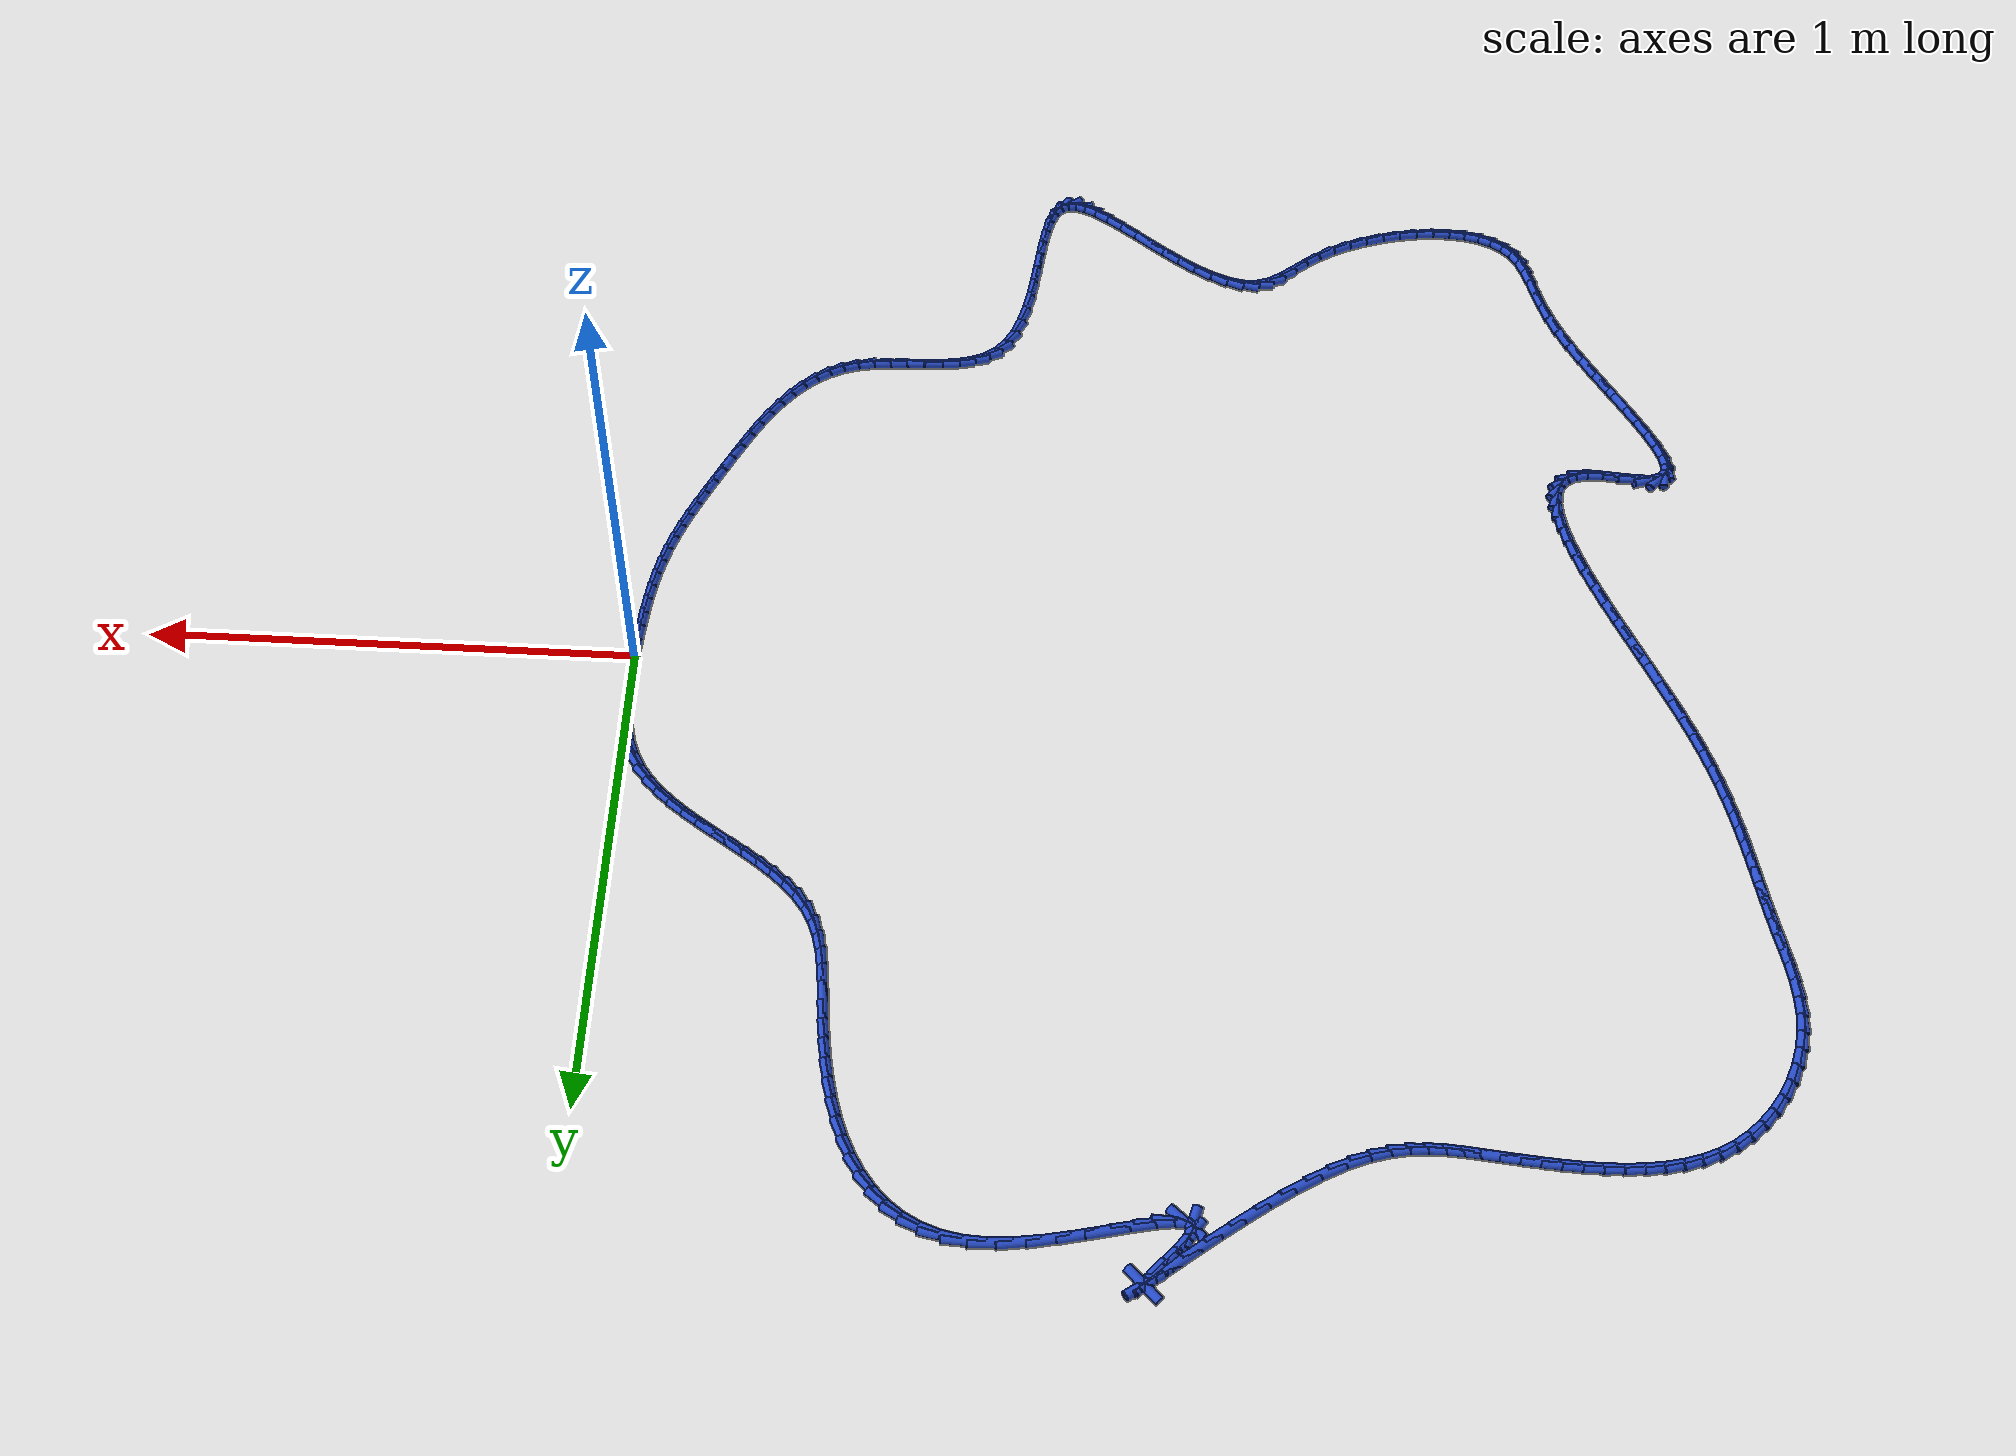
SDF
<sdf version="1.6">
 <world name="default">
  <light name="sun" type="directional">
   <pose>0 0 10 0 -0 0</pose>
   <diffuse>0.8 0.8 0.8 1</diffuse>
   <specular>0.2 0.2 0.2 1</specular>
   <attenuation>
    <range>1000</range>
    <constant>0.9</constant>
    <linear>0.01</linear>
    <quadratic>0.001</quadratic>
   </attenuation>
   <direction>-0.5 0.1 -0.9</direction>
  </light>
  <model name="ground_plane">
   <static>1</static>
   <link name="link">
    <collision name="collision">
     <geometry><plane><normal>0 0 1</normal><size>100 100</size></plane></geometry>
     <surface><friction><ode><mu>100</mu><mu2>50</mu2></ode></friction></surface>
    </collision>
    <visual name="visual">
     <cast_shadows>0</cast_shadows>
     <geometry><plane><normal>0 0 1</normal><size>100 100</size></plane></geometry>
     <material>
      <script><uri>file://media/materials/scripts/gazebo.material</uri><name>Gazebo/WhiteGlow</name></script>
     </material>
    </visual>
   </link>
  </model>
  <gravity>0 0 -9.8</gravity>
  <magnetic_field>6e-06 2.3e-05 -4.2e-05</magnetic_field>
  <atmosphere type="adiabatic"/>
  <physics name="default_physics" default="0" type="ode">
   <max_step_size>0.001</max_step_size>
   <real_time_factor>1</real_time_factor>
   <real_time_update_rate>1000</real_time_update_rate>
  </physics>
  <scene><ambient>0.4 0.4 0.4 1</ambient><background>0.7 0.7 0.7 1</background><shadows>1</shadows></scene>
  <spherical_coordinates>
   <surface_model>EARTH_WGS84</surface_model>
   <latitude_deg>0</latitude_deg>
   <longitude_deg>0</longitude_deg>
   <elevation>0</elevation>
   <heading_deg>0</heading_deg>
  </spherical_coordinates>
  <model name="line">
   <link name="link_0">
    <pose>-1.0408340855860843e-17 -8.326672684688674e-17 0.01 0 1.57 1.5297266263207427</pose>
    <collision name="collision">
     <geometry><cylinder><radius>0.01</radius><length>0.08</length></cylinder></geometry>
    </collision>
    <visual name="visual">
     <material>
      <script><name>Gazebo/Blue</name><uri>file://media/materials/scripts/gazebo.material</uri></script>
     </material>
     <geometry><cylinder><radius>0.01</radius><length>0.08</length></cylinder></geometry>
    </visual>
   </link>
   <link name="link_1">
    <pose>0.0014969408186911119 0.036428293038624965 0.01 0 1.57 1.5532019675587896</pose>
    <collision name="collision">
     <geometry><cylinder><radius>0.01</radius><length>0.08</length></cylinder></geometry>
    </collision>
    <visual name="visual">
     <material>
      <script><name>Gazebo/Blue</name><uri>file://media/materials/scripts/gazebo.material</uri></script>
     </material>
     <geometry><cylinder><radius>0.01</radius><length>0.08</length></cylinder></geometry>
    </visual>
   </link>
   <link name="link_2">
    <pose>0.0021394575937475698 0.07294286373632472 0.01 0 1.57 -1.5499854050380075</pose>
    <collision name="collision">
     <geometry><cylinder><radius>0.01</radius><length>0.08</length></cylinder></geometry>
    </collision>
    <visual name="visual">
     <material>
      <script><name>Gazebo/Blue</name><uri>file://media/materials/scripts/gazebo.material</uri></script>
     </material>
     <geometry><cylinder><radius>0.01</radius><length>0.08</length></cylinder></geometry>
    </visual>
   </link>
   <link name="link_3">
    <pose>0.001385550090561544 0.1091641647977159 0.01 0 1.57 -1.4952037405692213</pose>
    <collision name="collision">
     <geometry><cylinder><radius>0.01</radius><length>0.08</length></cylinder></geometry>
    </collision>
    <visual name="visual">
     <material>
      <script><name>Gazebo/Blue</name><uri>file://media/materials/scripts/gazebo.material</uri></script>
     </material>
     <geometry><cylinder><radius>0.01</radius><length>0.08</length></cylinder></geometry>
    </visual>
   </link>
   <link name="link_4">
    <pose>-0.0013067819254747844 0.14471264892741523 0.01 0 1.57 -1.4219534766089674</pose>
    <collision name="collision">
     <geometry><cylinder><radius>0.01</radius><length>0.08</length></cylinder></geometry>
    </collision>
    <visual name="visual">
     <material>
      <script><name>Gazebo/Blue</name><uri>file://media/materials/scripts/gazebo.material</uri></script>
     </material>
     <geometry><cylinder><radius>0.01</radius><length>0.08</length></cylinder></geometry>
    </visual>
   </link>
   <link name="link_5">
    <pose>-0.006479538688969233 0.17920876883003942 0.01 0 1.57 -1.3278360114464158</pose>
    <collision name="collision">
     <geometry><cylinder><radius>0.01</radius><length>0.08</length></cylinder></geometry>
    </collision>
    <visual name="visual">
     <material>
      <script><name>Gazebo/Blue</name><uri>file://media/materials/scripts/gazebo.material</uri></script>
     </material>
     <geometry><cylinder><radius>0.01</radius><length>0.08</length></cylinder></geometry>
    </visual>
   </link>
   <link name="link_6">
    <pose>-0.014674720434529626 0.21227297721020516 0.01 0 1.57 -1.2109089163713331</pose>
    <collision name="collision">
     <geometry><cylinder><radius>0.01</radius><length>0.08</length></cylinder></geometry>
    </collision>
    <visual name="visual">
     <material>
      <script><name>Gazebo/Blue</name><uri>file://media/materials/scripts/gazebo.material</uri></script>
     </material>
     <geometry><cylinder><radius>0.01</radius><length>0.08</length></cylinder></geometry>
    </visual>
   </link>
   <link name="link_7">
    <pose>-0.026434327396763775 0.24352572677252915 0.01 0 1.57 -1.0718549530865151</pose>
    <collision name="collision">
     <geometry><cylinder><radius>0.01</radius><length>0.08</length></cylinder></geometry>
    </collision>
    <visual name="visual">
     <material>
      <script><name>Gazebo/Blue</name><uri>file://media/materials/scripts/gazebo.material</uri></script>
     </material>
     <geometry><cylinder><radius>0.01</radius><length>0.08</length></cylinder></geometry>
    </visual>
   </link>
   <link name="link_8">
    <pose>-0.04227820942633523 0.2726008729582041 0.01 0 1.57 -0.9332765152744603</pose>
    <collision name="collision">
     <geometry><cylinder><radius>0.01</radius><length>0.08</length></cylinder></geometry>
    </collision>
    <visual name="visual">
     <material>
      <script><name>Gazebo/Blue</name><uri>file://media/materials/scripts/gazebo.material</uri></script>
     </material>
     <geometry><cylinder><radius>0.01</radius><length>0.08</length></cylinder></geometry>
    </visual>
   </link>
   <link name="link_9">
    <pose>-0.062176346499615294 0.29946498603155314 0.01 0 1.57 -0.8188629687761768</pose>
    <collision name="collision">
     <geometry><cylinder><radius>0.01</radius><length>0.08</length></cylinder></geometry>
    </collision>
    <visual name="visual">
     <material>
      <script><name>Gazebo/Blue</name><uri>file://media/materials/scripts/gazebo.material</uri></script>
     </material>
     <geometry><cylinder><radius>0.01</radius><length>0.08</length></cylinder></geometry>
    </visual>
   </link>
   <link name="link_10">
    <pose>-0.0855254146163852 0.32443153056787777 0.01 0 1.57 -0.7295507578301857</pose>
    <collision name="collision">
     <geometry><cylinder><radius>0.01</radius><length>0.08</length></cylinder></geometry>
    </collision>
    <visual name="visual">
     <material>
      <script><name>Gazebo/Blue</name><uri>file://media/materials/scripts/gazebo.material</uri></script>
     </material>
     <geometry><cylinder><radius>0.01</radius><length>0.08</length></cylinder></geometry>
    </visual>
   </link>
   <link name="link_11">
    <pose>-0.11169525001282593 0.34783021132514275 0.01 0 1.57 -0.6632890130271618</pose>
    <collision name="collision">
     <geometry><cylinder><radius>0.01</radius><length>0.08</length></cylinder></geometry>
    </collision>
    <visual name="visual">
     <material>
      <script><name>Gazebo/Blue</name><uri>file://media/materials/scripts/gazebo.material</uri></script>
     </material>
     <geometry><cylinder><radius>0.01</radius><length>0.08</length></cylinder></geometry>
    </visual>
   </link>
   <link name="link_12">
    <pose>-0.1400556889251184 0.36999073306131275 0.01 0 1.57 -0.6175890432596244</pose>
    <collision name="collision">
     <geometry><cylinder><radius>0.01</radius><length>0.08</length></cylinder></geometry>
    </collision>
    <visual name="visual">
     <material>
      <script><name>Gazebo/Blue</name><uri>file://media/materials/scripts/gazebo.material</uri></script>
     </material>
     <geometry><cylinder><radius>0.01</radius><length>0.08</length></cylinder></geometry>
    </visual>
   </link>
   <link name="link_13">
    <pose>-0.16997656758944332 0.3912428005343521 0.01 0 1.57 -0.5903748497441107</pose>
    <collision name="collision">
     <geometry><cylinder><radius>0.01</radius><length>0.08</length></cylinder></geometry>
    </collision>
    <visual name="visual">
     <material>
      <script><name>Gazebo/Blue</name><uri>file://media/materials/scripts/gazebo.material</uri></script>
     </material>
     <geometry><cylinder><radius>0.01</radius><length>0.08</length></cylinder></geometry>
    </visual>
   </link>
   <link name="link_14">
    <pose>-0.2008277222419817 0.4119161185022253 0.01 0 1.57 -0.5803356197771341</pose>
    <collision name="collision">
     <geometry><cylinder><radius>0.01</radius><length>0.08</length></cylinder></geometry>
    </collision>
    <visual name="visual">
     <material>
      <script><name>Gazebo/Blue</name><uri>file://media/materials/scripts/gazebo.material</uri></script>
     </material>
     <geometry><cylinder><radius>0.01</radius><length>0.08</length></cylinder></geometry>
    </visual>
   </link>
   <link name="link_15">
    <pose>-0.23197898911891446 0.4323403917228972 0.01 0 1.57 -0.5870463768068191</pose>
    <collision name="collision">
     <geometry><cylinder><radius>0.01</radius><length>0.08</length></cylinder></geometry>
    </collision>
    <visual name="visual">
     <material>
      <script><name>Gazebo/Blue</name><uri>file://media/materials/scripts/gazebo.material</uri></script>
     </material>
     <geometry><cylinder><radius>0.01</radius><length>0.08</length></cylinder></geometry>
    </visual>
   </link>
   <link name="link_16">
    <pose>-0.2628002044564224 0.45284532495433205 0.01 0 1.57 -0.6110090541003181</pose>
    <collision name="collision">
     <geometry><cylinder><radius>0.01</radius><length>0.08</length></cylinder></geometry>
    </collision>
    <visual name="visual">
     <material>
      <script><name>Gazebo/Blue</name><uri>file://media/materials/scripts/gazebo.material</uri></script>
     </material>
     <geometry><cylinder><radius>0.01</radius><length>0.08</length></cylinder></geometry>
    </visual>
   </link>
   <link name="link_17">
    <pose>-0.29266120449068644 0.4737606229544946 0.01 0 1.57 -0.6536643172534565</pose>
    <collision name="collision">
     <geometry><cylinder><radius>0.01</radius><length>0.08</length></cylinder></geometry>
    </collision>
    <visual name="visual">
     <material>
      <script><name>Gazebo/Blue</name><uri>file://media/materials/scripts/gazebo.material</uri></script>
     </material>
     <geometry><cylinder><radius>0.01</radius><length>0.08</length></cylinder></geometry>
    </visual>
   </link>
   <link name="link_18">
    <pose>-0.32093182545788745 0.4954159904813492 0.01 0 1.57 -0.7173349057130506</pose>
    <collision name="collision">
     <geometry><cylinder><radius>0.01</radius><length>0.08</length></cylinder></geometry>
    </collision>
    <visual name="visual">
     <material>
      <script><name>Gazebo/Blue</name><uri>file://media/materials/scripts/gazebo.material</uri></script>
     </material>
     <geometry><cylinder><radius>0.01</radius><length>0.08</length></cylinder></geometry>
    </visual>
   </link>
   <link name="link_19">
    <pose>-0.3469819035942063 0.5181411322928605 0.01 0 1.57 -0.8049470517846877</pose>
    <collision name="collision">
     <geometry><cylinder><radius>0.01</radius><length>0.08</length></cylinder></geometry>
    </collision>
    <visual name="visual">
     <material>
      <script><name>Gazebo/Blue</name><uri>file://media/materials/scripts/gazebo.material</uri></script>
     </material>
     <geometry><cylinder><radius>0.01</radius><length>0.08</length></cylinder></geometry>
    </visual>
   </link>
   <link name="link_20">
    <pose>-0.370181275135824 0.5422657531469931 0.01 0 1.57 -0.9192214256870803</pose>
    <collision name="collision">
     <geometry><cylinder><radius>0.01</radius><length>0.08</length></cylinder></geometry>
    </collision>
    <visual name="visual">
     <material>
      <script><name>Gazebo/Blue</name><uri>file://media/materials/scripts/gazebo.material</uri></script>
     </material>
     <geometry><cylinder><radius>0.01</radius><length>0.08</length></cylinder></geometry>
    </visual>
   </link>
   <link name="link_21">
    <pose>-0.3898997763189213 0.5681195578017115 0.01 0 1.57 -1.0607809543851017</pose>
    <collision name="collision">
     <geometry><cylinder><radius>0.01</radius><length>0.08</length></cylinder></geometry>
    </collision>
    <visual name="visual">
     <material>
      <script><name>Gazebo/Blue</name><uri>file://media/materials/scripts/gazebo.material</uri></script>
     </material>
     <geometry><cylinder><radius>0.01</radius><length>0.08</length></cylinder></geometry>
    </visual>
   </link>
   <link name="link_22">
    <pose>-0.40551247960679276 0.5960303412513841 0.01 0 1.57 -1.2092258562447675</pose>
    <collision name="collision">
     <geometry><cylinder><radius>0.01</radius><length>0.08</length></cylinder></geometry>
    </collision>
    <visual name="visual">
     <material>
      <script><name>Gazebo/Blue</name><uri>file://media/materials/scripts/gazebo.material</uri></script>
     </material>
     <geometry><cylinder><radius>0.01</radius><length>0.08</length></cylinder></geometry>
    </visual>
   </link>
   <link name="link_23">
    <pose>-0.41690037989489975 0.6261413777997294 0.01 0 1.57 -1.32772804652969</pose>
    <collision name="collision">
     <geometry><cylinder><radius>0.01</radius><length>0.08</length></cylinder></geometry>
    </collision>
    <visual name="visual">
     <material>
      <script><name>Gazebo/Blue</name><uri>file://media/materials/scripts/gazebo.material</uri></script>
     </material>
     <geometry><cylinder><radius>0.01</radius><length>0.08</length></cylinder></geometry>
    </visual>
   </link>
   <link name="link_24">
    <pose>-0.42486493000674563 0.6582602311320055 0.01 0 1.57 -1.4116682011349573</pose>
    <collision name="collision">
     <geometry><cylinder><radius>0.01</radius><length>0.08</length></cylinder></geometry>
    </collision>
    <visual name="visual">
     <material>
      <script><name>Gazebo/Blue</name><uri>file://media/materials/scripts/gazebo.material</uri></script>
     </material>
     <geometry><cylinder><radius>0.01</radius><length>0.08</length></cylinder></geometry>
    </visual>
   </link>
   <link name="link_25">
    <pose>-0.43030515460128826 0.6921588784061253 0.01 0 1.57 -1.463595929834976</pose>
    <collision name="collision">
     <geometry><cylinder><radius>0.01</radius><length>0.08</length></cylinder></geometry>
    </collision>
    <visual name="visual">
     <material>
      <script><name>Gazebo/Blue</name><uri>file://media/materials/scripts/gazebo.material</uri></script>
     </material>
     <geometry><cylinder><radius>0.01</radius><length>0.08</length></cylinder></geometry>
    </visual>
   </link>
   <link name="link_26">
    <pose>-0.4341200783374854 0.7276092967800031 0.01 0 1.57 -1.4870033899448325</pose>
    <collision name="collision">
     <geometry><cylinder><radius>0.01</radius><length>0.08</length></cylinder></geometry>
    </collision>
    <visual name="visual">
     <material>
      <script><name>Gazebo/Blue</name><uri>file://media/materials/scripts/gazebo.material</uri></script>
     </material>
     <geometry><cylinder><radius>0.01</radius><length>0.08</length></cylinder></geometry>
    </visual>
   </link>
   <link name="link_27">
    <pose>-0.4372087258742949 0.7643834634115524 0.01 0 1.57 -1.4848872198881395</pose>
    <collision name="collision">
     <geometry><cylinder><radius>0.01</radius><length>0.08</length></cylinder></geometry>
    </collision>
    <visual name="visual">
     <material>
      <script><name>Gazebo/Blue</name><uri>file://media/materials/scripts/gazebo.material</uri></script>
     </material>
     <geometry><cylinder><radius>0.01</radius><length>0.08</length></cylinder></geometry>
    </visual>
   </link>
   <link name="link_28">
    <pose>-0.4404701218706746 0.8022533554586873 0.01 0 1.57 -1.46141886753978</pose>
    <collision name="collision">
     <geometry><cylinder><radius>0.01</radius><length>0.08</length></cylinder></geometry>
    </collision>
    <visual name="visual">
     <material>
      <script><name>Gazebo/Blue</name><uri>file://media/materials/scripts/gazebo.material</uri></script>
     </material>
     <geometry><cylinder><radius>0.01</radius><length>0.08</length></cylinder></geometry>
    </visual>
   </link>
   <link name="link_29">
    <pose>-0.4447207933494986 0.8409606641183603 0.01 0 1.57 -1.4280645154312355</pose>
    <collision name="collision">
     <geometry><cylinder><radius>0.01</radius><length>0.08</length></cylinder></geometry>
    </collision>
    <visual name="visual">
     <material>
      <script><name>Gazebo/Blue</name><uri>file://media/materials/scripts/gazebo.material</uri></script>
     </material>
     <geometry><cylinder><radius>0.01</radius><length>0.08</length></cylinder></geometry>
    </visual>
   </link>
   <link name="link_30">
    <pose>-0.4503437343347484 0.8800879249546718 0.01 0 1.57 -1.3876931762479712</pose>
    <collision name="collision">
     <geometry><cylinder><radius>0.01</radius><length>0.08</length></cylinder></geometry>
    </collision>
    <visual name="visual">
     <material>
      <script><name>Gazebo/Blue</name><uri>file://media/materials/scripts/gazebo.material</uri></script>
     </material>
     <geometry><cylinder><radius>0.01</radius><length>0.08</length></cylinder></geometry>
    </visual>
   </link>
   <link name="link_31">
    <pose>-0.4575800264406972 0.9191655756304437 0.01 0 1.57 -1.3392617157119997</pose>
    <collision name="collision">
     <geometry><cylinder><radius>0.01</radius><length>0.08</length></cylinder></geometry>
    </collision>
    <visual name="visual">
     <material>
      <script><name>Gazebo/Blue</name><uri>file://media/materials/scripts/gazebo.material</uri></script>
     </material>
     <geometry><cylinder><radius>0.01</radius><length>0.08</length></cylinder></geometry>
    </visual>
   </link>
   <link name="link_32">
    <pose>-0.46667066988374883 0.9577240239262774 0.01 0 1.57 -1.2814140601729507</pose>
    <collision name="collision">
     <geometry><cylinder><radius>0.01</radius><length>0.08</length></cylinder></geometry>
    </collision>
    <visual name="visual">
     <material>
      <script><name>Gazebo/Blue</name><uri>file://media/materials/scripts/gazebo.material</uri></script>
     </material>
     <geometry><cylinder><radius>0.01</radius><length>0.08</length></cylinder></geometry>
    </visual>
   </link>
   <link name="link_33">
    <pose>-0.47785666488030637 0.9952936776227727 0.01 0 1.57 -1.2124962077877541</pose>
    <collision name="collision">
     <geometry><cylinder><radius>0.01</radius><length>0.08</length></cylinder></geometry>
    </collision>
    <visual name="visual">
     <material>
      <script><name>Gazebo/Blue</name><uri>file://media/materials/scripts/gazebo.material</uri></script>
     </material>
     <geometry><cylinder><radius>0.01</radius><length>0.08</length></cylinder></geometry>
    </visual>
   </link>
   <link name="link_34">
    <pose>-0.4913790116467733 1.0314049445005296 0.01 0 1.57 -1.1306317666146155</pose>
    <collision name="collision">
     <geometry><cylinder><radius>0.01</radius><length>0.08</length></cylinder></geometry>
    </collision>
    <visual name="visual">
     <material>
      <script><name>Gazebo/Blue</name><uri>file://media/materials/scripts/gazebo.material</uri></script>
     </material>
     <geometry><cylinder><radius>0.01</radius><length>0.08</length></cylinder></geometry>
    </visual>
   </link>
   <link name="link_35">
    <pose>-0.5074787103995532 1.0655882323401487 0.01 0 1.57 -1.0339324738233127</pose>
    <collision name="collision">
     <geometry><cylinder><radius>0.01</radius><length>0.08</length></cylinder></geometry>
    </collision>
    <visual name="visual">
     <material>
      <script><name>Gazebo/Blue</name><uri>file://media/materials/scripts/gazebo.material</uri></script>
     </material>
     <geometry><cylinder><radius>0.01</radius><length>0.08</length></cylinder></geometry>
    </visual>
   </link>
   <link name="link_36">
    <pose>-0.5263967613550492 1.0973739489222303 0.01 0 1.57 -0.9209411549852236</pose>
    <collision name="collision">
     <geometry><cylinder><radius>0.01</radius><length>0.08</length></cylinder></geometry>
    </collision>
    <visual name="visual">
     <material>
      <script><name>Gazebo/Blue</name><uri>file://media/materials/scripts/gazebo.material</uri></script>
     </material>
     <geometry><cylinder><radius>0.01</radius><length>0.08</length></cylinder></geometry>
    </visual>
   </link>
   <link name="link_37">
    <pose>-0.548374164729665 1.1262925020273746 0.01 0 1.57 -0.7913761509424856</pose>
    <collision name="collision">
     <geometry><cylinder><radius>0.01</radius><length>0.08</length></cylinder></geometry>
    </collision>
    <visual name="visual">
     <material>
      <script><name>Gazebo/Blue</name><uri>file://media/materials/scripts/gazebo.material</uri></script>
     </material>
     <geometry><cylinder><radius>0.01</radius><length>0.08</length></cylinder></geometry>
    </visual>
   </link>
   <link name="link_38">
    <pose>-0.573651920739804 1.151874299436182 0.01 0 1.57 -0.6470695402236666</pose>
    <collision name="collision">
     <geometry><cylinder><radius>0.01</radius><length>0.08</length></cylinder></geometry>
    </collision>
    <visual name="visual">
     <material>
      <script><name>Gazebo/Blue</name><uri>file://media/materials/scripts/gazebo.material</uri></script>
     </material>
     <geometry><cylinder><radius>0.01</radius><length>0.08</length></cylinder></geometry>
    </visual>
   </link>
   <link name="link_39">
    <pose>-0.6024710296018695 1.1736497489292526 0.01 0 1.57 -0.492629651869623</pose>
    <collision name="collision">
     <geometry><cylinder><radius>0.01</radius><length>0.08</length></cylinder></geometry>
    </collision>
    <visual name="visual">
     <material>
      <script><name>Gazebo/Blue</name><uri>file://media/materials/scripts/gazebo.material</uri></script>
     </material>
     <geometry><cylinder><radius>0.01</radius><length>0.08</length></cylinder></geometry>
    </visual>
   </link>
   <link name="link_40">
    <pose>-0.6350724915322651 1.1911492582871874 0.01 0 1.57 -0.3350999762518501</pose>
    <collision name="collision">
     <geometry><cylinder><radius>0.01</radius><length>0.08</length></cylinder></geometry>
    </collision>
    <visual name="visual">
     <material>
      <script><name>Gazebo/Blue</name><uri>file://media/materials/scripts/gazebo.material</uri></script>
     </material>
     <geometry><cylinder><radius>0.01</radius><length>0.08</length></cylinder></geometry>
    </visual>
   </link>
   <link name="link_41">
    <pose>-0.6716973067473939 1.2039032352905856 0.01 0 1.57 -0.18232529884809962</pose>
    <collision name="collision">
     <geometry><cylinder><radius>0.01</radius><length>0.08</length></cylinder></geometry>
    </collision>
    <visual name="visual">
     <material>
      <script><name>Gazebo/Blue</name><uri>file://media/materials/scripts/gazebo.material</uri></script>
     </material>
     <geometry><cylinder><radius>0.01</radius><length>0.08</length></cylinder></geometry>
    </visual>
   </link>
   <link name="link_42">
    <pose>-0.7125864754636595 1.2114420877200485 0.01 0 1.57 -0.040905578266627024</pose>
    <collision name="collision">
     <geometry><cylinder><radius>0.01</radius><length>0.08</length></cylinder></geometry>
    </collision>
    <visual name="visual">
     <material>
      <script><name>Gazebo/Blue</name><uri>file://media/materials/scripts/gazebo.material</uri></script>
     </material>
     <geometry><cylinder><radius>0.01</radius><length>0.08</length></cylinder></geometry>
    </visual>
   </link>
   <link name="link_43">
    <pose>-0.7579769598924062 1.2132998480249382 0.01 0 1.57 0.07429336983838616</pose>
    <collision name="collision">
     <geometry><cylinder><radius>0.01</radius><length>0.08</length></cylinder></geometry>
    </collision>
    <visual name="visual">
     <material>
      <script><name>Gazebo/Blue</name><uri>file://media/materials/scripts/gazebo.material</uri></script>
     </material>
     <geometry><cylinder><radius>0.01</radius><length>0.08</length></cylinder></geometry>
    </visual>
   </link>
   <link name="link_44">
    <pose>-0.8074276463970875 1.2096192156345396 0.01 0 1.57 0.1497238501654045</pose>
    <collision name="collision">
     <geometry><cylinder><radius>0.01</radius><length>0.08</length></cylinder></geometry>
    </collision>
    <visual name="visual">
     <material>
      <script><name>Gazebo/Blue</name><uri>file://media/materials/scripts/gazebo.material</uri></script>
     </material>
     <geometry><cylinder><radius>0.01</radius><length>0.08</length></cylinder></geometry>
    </visual>
   </link>
   <link name="link_45">
    <pose>-0.859063806638081 1.2018297577148511 0.01 0 1.57 0.19650721051475933</pose>
    <collision name="collision">
     <geometry><cylinder><radius>0.01</radius><length>0.08</length></cylinder></geometry>
    </collision>
    <visual name="visual">
     <material>
      <script><name>Gazebo/Blue</name><uri>file://media/materials/scripts/gazebo.material</uri></script>
     </material>
     <geometry><cylinder><radius>0.01</radius><length>0.08</length></cylinder></geometry>
    </visual>
   </link>
   <link name="link_46">
    <pose>-0.9108284528862703 1.1915246444749679 0.01 0 1.57 0.22159070632483877</pose>
    <collision name="collision">
     <geometry><cylinder><radius>0.01</radius><length>0.08</length></cylinder></geometry>
    </collision>
    <visual name="visual">
     <material>
      <script><name>Gazebo/Blue</name><uri>file://media/materials/scripts/gazebo.material</uri></script>
     </material>
     <geometry><cylinder><radius>0.01</radius><length>0.08</length></cylinder></geometry>
    </visual>
   </link>
   <link name="link_47">
    <pose>-0.9606645974125405 1.1802970461239826 0.01 0 1.57 0.2263016704757438</pose>
    <collision name="collision">
     <geometry><cylinder><radius>0.01</radius><length>0.08</length></cylinder></geometry>
    </collision>
    <visual name="visual">
     <material>
      <script><name>Gazebo/Blue</name><uri>file://media/materials/scripts/gazebo.material</uri></script>
     </material>
     <geometry><cylinder><radius>0.01</radius><length>0.08</length></cylinder></geometry>
    </visual>
   </link>
   <link name="link_48">
    <pose>-1.0065152524877758 1.1697401328709907 0.01 0 1.57 0.2053878668074822</pose>
    <collision name="collision">
     <geometry><cylinder><radius>0.01</radius><length>0.08</length></cylinder></geometry>
    </collision>
    <visual name="visual">
     <material>
      <script><name>Gazebo/Blue</name><uri>file://media/materials/scripts/gazebo.material</uri></script>
     </material>
     <geometry><cylinder><radius>0.01</radius><length>0.08</length></cylinder></geometry>
    </visual>
   </link>
   <link name="link_49">
    <pose>-1.0463234303828606 1.161447074925087 0.01 0 1.57 0.13899735155981005</pose>
    <collision name="collision">
     <geometry><cylinder><radius>0.01</radius><length>0.08</length></cylinder></geometry>
    </collision>
    <visual name="visual">
     <material>
      <script><name>Gazebo/Blue</name><uri>file://media/materials/scripts/gazebo.material</uri></script>
     </material>
     <geometry><cylinder><radius>0.01</radius><length>0.08</length></cylinder></geometry>
    </visual>
   </link>
   <link name="link_50">
    <pose>-1.0780321433686788 1.157011042495364 0.01 0 1.57 -0.047021320692922385</pose>
    <collision name="collision">
     <geometry><cylinder><radius>0.01</radius><length>0.08</length></cylinder></geometry>
    </collision>
    <visual name="visual">
     <material>
      <script><name>Gazebo/Blue</name><uri>file://media/materials/scripts/gazebo.material</uri></script>
     </material>
     <geometry><cylinder><radius>0.01</radius><length>0.08</length></cylinder></geometry>
    </visual>
   </link>
   <link name="link_51">
    <pose>-1.0995844037161158 1.158025205790918 0.01 0 1.57 -0.7118780612363667</pose>
    <collision name="collision">
     <geometry><cylinder><radius>0.01</radius><length>0.08</length></cylinder></geometry>
    </collision>
    <visual name="visual">
     <material>
      <script><name>Gazebo/Blue</name><uri>file://media/materials/scripts/gazebo.material</uri></script>
     </material>
     <geometry><cylinder><radius>0.01</radius><length>0.08</length></cylinder></geometry>
    </visual>
   </link>
   <link name="link_52">
    <pose>-1.1089232236960553 1.1660827350208425 0.01 0 1.57 1.2835550571192555</pose>
    <collision name="collision">
     <geometry><cylinder><radius>0.01</radius><length>0.08</length></cylinder></geometry>
    </collision>
    <visual name="visual">
     <material>
      <script><name>Gazebo/Blue</name><uri>file://media/materials/scripts/gazebo.material</uri></script>
     </material>
     <geometry><cylinder><radius>0.01</radius><length>0.08</length></cylinder></geometry>
    </visual>
   </link>
   <link name="link_53">
    <pose>-1.1039916155793819 1.1827768003942316 0.01 0 1.57 0.9191735991039887</pose>
    <collision name="collision">
     <geometry><cylinder><radius>0.01</radius><length>0.08</length></cylinder></geometry>
    </collision>
    <visual name="visual">
     <material>
      <script><name>Gazebo/Blue</name><uri>file://media/materials/scripts/gazebo.material</uri></script>
     </material>
     <geometry><cylinder><radius>0.01</radius><length>0.08</length></cylinder></geometry>
    </visual>
   </link>
   <link name="link_54">
    <pose>-1.0844636825280243 1.2083782033325576 0.01 0 1.57 0.8265547010551558</pose>
    <collision name="collision">
     <geometry><cylinder><radius>0.01</radius><length>0.08</length></cylinder></geometry>
    </collision>
    <visual name="visual">
     <material>
      <script><name>Gazebo/Blue</name><uri>file://media/materials/scripts/gazebo.material</uri></script>
     </material>
     <geometry><cylinder><radius>0.01</radius><length>0.08</length></cylinder></geometry>
    </visual>
   </link>
   <link name="link_55">
    <pose>-1.0581804298343038 1.2369191031821296 0.01 0 1.57 0.8044011865111247</pose>
    <collision name="collision">
     <geometry><cylinder><radius>0.01</radius><length>0.08</length></cylinder></geometry>
    </collision>
    <visual name="visual">
     <material>
      <script><name>Gazebo/Blue</name><uri>file://media/materials/scripts/gazebo.material</uri></script>
     </material>
     <geometry><cylinder><radius>0.01</radius><length>0.08</length></cylinder></geometry>
    </visual>
   </link>
   <link name="link_56">
    <pose>-1.0353890214815114 1.2605936107110665 0.01 0 1.57 0.8521151460480642</pose>
    <collision name="collision">
     <geometry><cylinder><radius>0.01</radius><length>0.08</length></cylinder></geometry>
    </collision>
    <visual name="visual">
     <material>
      <script><name>Gazebo/Blue</name><uri>file://media/materials/scripts/gazebo.material</uri></script>
     </material>
     <geometry><cylinder><radius>0.01</radius><length>0.08</length></cylinder></geometry>
    </visual>
   </link>
   <link name="link_57">
    <pose>-1.0244231020954433 1.2731298540933953 0.01 0 1.57 -0.8008958933208356</pose>
    <collision name="collision">
     <geometry><cylinder><radius>0.01</radius><length>0.08</length></cylinder></geometry>
    </collision>
    <visual name="visual">
     <material>
      <script><name>Gazebo/Blue</name><uri>file://media/materials/scripts/gazebo.material</uri></script>
     </material>
     <geometry><cylinder><radius>0.01</radius><length>0.08</length></cylinder></geometry>
    </visual>
   </link>
   <link name="link_58">
    <pose>-1.0257846910530326 1.274534313960926 0.01 0 1.57 0.5874172456001568</pose>
    <collision name="collision">
     <geometry><cylinder><radius>0.01</radius><length>0.08</length></cylinder></geometry>
    </collision>
    <visual name="visual">
     <material>
      <script><name>Gazebo/Blue</name><uri>file://media/materials/scripts/gazebo.material</uri></script>
     </material>
     <geometry><cylinder><radius>0.01</radius><length>0.08</length></cylinder></geometry>
    </visual>
   </link>
   <link name="link_59">
    <pose>-1.037972845127066 1.2664191791846888 0.01 0 1.57 0.6401372926653841</pose>
    <collision name="collision">
     <geometry><cylinder><radius>0.01</radius><length>0.08</length></cylinder></geometry>
    </collision>
    <visual name="visual">
     <material>
      <script><name>Gazebo/Blue</name><uri>file://media/materials/scripts/gazebo.material</uri></script>
     </material>
     <geometry><cylinder><radius>0.01</radius><length>0.08</length></cylinder></geometry>
    </visual>
   </link>
   <link name="link_60">
    <pose>-1.059486620236054 1.250396639320557 0.01 0 1.57 0.650313901921996</pose>
    <collision name="collision">
     <geometry><cylinder><radius>0.01</radius><length>0.08</length></cylinder></geometry>
    </collision>
    <visual name="visual">
     <material>
      <script><name>Gazebo/Blue</name><uri>file://media/materials/scripts/gazebo.material</uri></script>
     </material>
     <geometry><cylinder><radius>0.01</radius><length>0.08</length></cylinder></geometry>
    </visual>
   </link>
   <link name="link_61">
    <pose>-1.0888250722985071 1.2280788839244055 0.01 0 1.57 0.6480464195855881</pose>
    <collision name="collision">
     <geometry><cylinder><radius>0.01</radius><length>0.08</length></cylinder></geometry>
    </collision>
    <visual name="visual">
     <material>
      <script><name>Gazebo/Blue</name><uri>file://media/materials/scripts/gazebo.material</uri></script>
     </material>
     <geometry><cylinder><radius>0.01</radius><length>0.08</length></cylinder></geometry>
    </visual>
   </link>
   <link name="link_62">
    <pose>-1.1244872572329374 1.2010781025521085 0.01 0 1.57 0.6388672811564012</pose>
    <collision name="collision">
     <geometry><cylinder><radius>0.01</radius><length>0.08</length></cylinder></geometry>
    </collision>
    <visual name="visual">
     <material>
      <script><name>Gazebo/Blue</name><uri>file://media/materials/scripts/gazebo.material</uri></script>
     </material>
     <geometry><cylinder><radius>0.01</radius><length>0.08</length></cylinder></geometry>
    </visual>
   </link>
   <link name="link_63">
    <pose>-1.1649722309578554 1.1710064847595392 0.01 0 1.57 0.6238630042924764</pose>
    <collision name="collision">
     <geometry><cylinder><radius>0.01</radius><length>0.08</length></cylinder></geometry>
    </collision>
    <visual name="visual">
     <material>
      <script><name>Gazebo/Blue</name><uri>file://media/materials/scripts/gazebo.material</uri></script>
     </material>
     <geometry><cylinder><radius>0.01</radius><length>0.08</length></cylinder></geometry>
    </visual>
   </link>
   <link name="link_64">
    <pose>-1.208779049391771 1.1394762201025725 0.01 0 1.57 0.602401411614445</pose>
    <collision name="collision">
     <geometry><cylinder><radius>0.01</radius><length>0.08</length></cylinder></geometry>
    </collision>
    <visual name="visual">
     <material>
      <script><name>Gazebo/Blue</name><uri>file://media/materials/scripts/gazebo.material</uri></script>
     </material>
     <geometry><cylinder><radius>0.01</radius><length>0.08</length></cylinder></geometry>
    </visual>
   </link>
   <link name="link_65">
    <pose>-1.2544067684531965 1.1080994981370824 0.01 0 1.57 0.5724638955727281</pose>
    <collision name="collision">
     <geometry><cylinder><radius>0.01</radius><length>0.08</length></cylinder></geometry>
    </collision>
    <visual name="visual">
     <material>
      <script><name>Gazebo/Blue</name><uri>file://media/materials/scripts/gazebo.material</uri></script>
     </material>
     <geometry><cylinder><radius>0.01</radius><length>0.08</length></cylinder></geometry>
    </visual>
   </link>
   <link name="link_66">
    <pose>-1.3003544440606425 1.0784885084189424 0.01 0 1.57 0.5300582631437174</pose>
    <collision name="collision">
     <geometry><cylinder><radius>0.01</radius><length>0.08</length></cylinder></geometry>
    </collision>
    <visual name="visual">
     <material>
      <script><name>Gazebo/Blue</name><uri>file://media/materials/scripts/gazebo.material</uri></script>
     </material>
     <geometry><cylinder><radius>0.01</radius><length>0.08</length></cylinder></geometry>
    </visual>
   </link>
   <link name="link_67">
    <pose>-1.3451211321326193 1.0522554405040274 0.01 0 1.57 0.46765626670080074</pose>
    <collision name="collision">
     <geometry><cylinder><radius>0.01</radius><length>0.08</length></cylinder></geometry>
    </collision>
    <visual name="visual">
     <material>
      <script><name>Gazebo/Blue</name><uri>file://media/materials/scripts/gazebo.material</uri></script>
     </material>
     <geometry><cylinder><radius>0.01</radius><length>0.08</length></cylinder></geometry>
    </visual>
   </link>
   <link name="link_68">
    <pose>-1.3872240800891007 1.0309925713047705 0.01 0 1.57 0.3829734330935997</pose>
    <collision name="collision">
     <geometry><cylinder><radius>0.01</radius><length>0.08</length></cylinder></geometry>
    </collision>
    <visual name="visual">
     <material>
      <script><name>Gazebo/Blue</name><uri>file://media/materials/scripts/gazebo.material</uri></script>
     </material>
     <geometry><cylinder><radius>0.01</radius><length>0.08</length></cylinder></geometry>
    </visual>
   </link>
   <link name="link_69">
    <pose>-1.4260347762476588 1.0153571150373355 0.01 0 1.57 0.28738206447069775</pose>
    <collision name="collision">
     <geometry><cylinder><radius>0.01</radius><length>0.08</length></cylinder></geometry>
    </collision>
    <visual name="visual">
     <material>
      <script><name>Gazebo/Blue</name><uri>file://media/materials/scripts/gazebo.material</uri></script>
     </material>
     <geometry><cylinder><radius>0.01</radius><length>0.08</length></cylinder></geometry>
    </visual>
   </link>
   <link name="link_70">
    <pose>-1.4621278611275925 1.004689300574609 0.01 0 1.57 0.1875162440671363</pose>
    <collision name="collision">
     <geometry><cylinder><radius>0.01</radius><length>0.08</length></cylinder></geometry>
    </collision>
    <visual name="visual">
     <material>
      <script><name>Gazebo/Blue</name><uri>file://media/materials/scripts/gazebo.material</uri></script>
     </material>
     <geometry><cylinder><radius>0.01</radius><length>0.08</length></cylinder></geometry>
    </visual>
   </link>
   <link name="link_71">
    <pose>-1.4961685250682584 0.998230239831801 0.01 0 1.57 0.09189598982674581</pose>
    <collision name="collision">
     <geometry><cylinder><radius>0.01</radius><length>0.08</length></cylinder></geometry>
    </collision>
    <visual name="visual">
     <material>
      <script><name>Gazebo/Blue</name><uri>file://media/materials/scripts/gazebo.material</uri></script>
     </material>
     <geometry><cylinder><radius>0.01</radius><length>0.08</length></cylinder></geometry>
    </visual>
   </link>
   <link name="link_72">
    <pose>-1.5288219584090146 0.9952210447241225 0.01 0 1.57 0.009965334823651088</pose>
    <collision name="collision">
     <geometry><cylinder><radius>0.01</radius><length>0.08</length></cylinder></geometry>
    </collision>
    <visual name="visual">
     <material>
      <script><name>Gazebo/Blue</name><uri>file://media/materials/scripts/gazebo.material</uri></script>
     </material>
     <geometry><cylinder><radius>0.01</radius><length>0.08</length></cylinder></geometry>
    </visual>
   </link>
   <link name="link_73">
    <pose>-1.5607533514892191 0.994902827166784 0.01 0 1.57 -0.05058880092744485</pose>
    <collision name="collision">
     <geometry><cylinder><radius>0.01</radius><length>0.08</length></cylinder></geometry>
    </collision>
    <visual name="visual">
     <material>
      <script><name>Gazebo/Blue</name><uri>file://media/materials/scripts/gazebo.material</uri></script>
     </material>
     <geometry><cylinder><radius>0.01</radius><length>0.08</length></cylinder></geometry>
    </visual>
   </link>
   <link name="link_74">
    <pose>-1.59262789464823 0.9965166990749962 0.01 0 1.57 -0.08559166201118545</pose>
    <collision name="collision">
     <geometry><cylinder><radius>0.01</radius><length>0.08</length></cylinder></geometry>
    </collision>
    <visual name="visual">
     <material>
      <script><name>Gazebo/Blue</name><uri>file://media/materials/scripts/gazebo.material</uri></script>
     </material>
     <geometry><cylinder><radius>0.01</radius><length>0.08</length></cylinder></geometry>
    </visual>
   </link>
   <link name="link_75">
    <pose>-1.6251107782254048 0.9993037723639695 0.01 0 1.57 -0.09699294355219688</pose>
    <collision name="collision">
     <geometry><cylinder><radius>0.01</radius><length>0.08</length></cylinder></geometry>
    </collision>
    <visual name="visual">
     <material>
      <script><name>Gazebo/Blue</name><uri>file://media/materials/scripts/gazebo.material</uri></script>
     </material>
     <geometry><cylinder><radius>0.01</radius><length>0.08</length></cylinder></geometry>
    </visual>
   </link>
   <link name="link_76">
    <pose>-1.6587249623088898 1.0025743736650434 0.01 0 1.57 -0.09657853734811621</pose>
    <collision name="collision">
     <geometry><cylinder><radius>0.01</radius><length>0.08</length></cylinder></geometry>
    </collision>
    <visual name="visual">
     <material>
      <script><name>Gazebo/Blue</name><uri>file://media/materials/scripts/gazebo.material</uri></script>
     </material>
     <geometry><cylinder><radius>0.01</radius><length>0.08</length></cylinder></geometry>
    </visual>
   </link>
   <link name="link_77">
    <pose>-1.693389572106803 1.005932678909928 0.01 0 1.57 -0.0879541873327349</pose>
    <collision name="collision">
     <geometry><cylinder><radius>0.01</radius><length>0.08</length></cylinder></geometry>
    </collision>
    <visual name="visual">
     <material>
      <script><name>Gazebo/Blue</name><uri>file://media/materials/scripts/gazebo.material</uri></script>
     </material>
     <geometry><cylinder><radius>0.01</radius><length>0.08</length></cylinder></geometry>
    </visual>
   </link>
   <link name="link_78">
    <pose>-1.7288635165709654 1.0090608314290013 0.01 0 1.57 -0.0714648572897058</pose>
    <collision name="collision">
     <geometry><cylinder><radius>0.01</radius><length>0.08</length></cylinder></geometry>
    </collision>
    <visual name="visual">
     <material>
      <script><name>Gazebo/Blue</name><uri>file://media/materials/scripts/gazebo.material</uri></script>
     </material>
     <geometry><cylinder><radius>0.01</radius><length>0.08</length></cylinder></geometry>
    </visual>
   </link>
   <link name="link_79">
    <pose>-1.7649057034720708 1.0116409751274225 0.01 0 1.57 -0.04710041621450012</pose>
    <collision name="collision">
     <geometry><cylinder><radius>0.01</radius><length>0.08</length></cylinder></geometry>
    </collision>
    <visual name="visual">
     <material>
      <script><name>Gazebo/Blue</name><uri>file://media/materials/scripts/gazebo.material</uri></script>
     </material>
     <geometry><cylinder><radius>0.01</radius><length>0.08</length></cylinder></geometry>
    </visual>
   </link>
   <link name="link_80">
    <pose>-1.801275040580813 1.0133552539103508 0.01 0 1.57 -0.014552587274043826</pose>
    <collision name="collision">
     <geometry><cylinder><radius>0.01</radius><length>0.08</length></cylinder></geometry>
    </collision>
    <visual name="visual">
     <material>
      <script><name>Gazebo/Blue</name><uri>file://media/materials/scripts/gazebo.material</uri></script>
     </material>
     <geometry><cylinder><radius>0.01</radius><length>0.08</length></cylinder></geometry>
    </visual>
   </link>
   <link name="link_81">
    <pose>-1.8377304356678852 1.013885811682946 0.01 0 1.57 0.026743200578914498</pose>
    <collision name="collision">
     <geometry><cylinder><radius>0.01</radius><length>0.08</length></cylinder></geometry>
    </collision>
    <visual name="visual">
     <material>
      <script><name>Gazebo/Blue</name><uri>file://media/materials/scripts/gazebo.material</uri></script>
     </material>
     <geometry><cylinder><radius>0.01</radius><length>0.08</length></cylinder></geometry>
    </visual>
   </link>
   <link name="link_82">
    <pose>-1.8740307965039829 1.0129147923503679 0.01 0 1.57 0.07756339814384612</pose>
    <collision name="collision">
     <geometry><cylinder><radius>0.01</radius><length>0.08</length></cylinder></geometry>
    </collision>
    <visual name="visual">
     <material>
      <script><name>Gazebo/Blue</name><uri>file://media/materials/scripts/gazebo.material</uri></script>
     </material>
     <geometry><cylinder><radius>0.01</radius><length>0.08</length></cylinder></geometry>
    </visual>
   </link>
   <link name="link_83">
    <pose>-1.9099350308597987 1.0101243398177757 0.01 0 1.57 0.13882783263708748</pose>
    <collision name="collision">
     <geometry><cylinder><radius>0.01</radius><length>0.08</length></cylinder></geometry>
    </collision>
    <visual name="visual">
     <material>
      <script><name>Gazebo/Blue</name><uri>file://media/materials/scripts/gazebo.material</uri></script>
     </material>
     <geometry><cylinder><radius>0.01</radius><length>0.08</length></cylinder></geometry>
    </visual>
   </link>
   <link name="link_84">
    <pose>-1.945202046506027 1.0051965979903295 0.01 0 1.57 0.21147917627916138</pose>
    <collision name="collision">
     <geometry><cylinder><radius>0.01</radius><length>0.08</length></cylinder></geometry>
    </collision>
    <visual name="visual">
     <material>
      <script><name>Gazebo/Blue</name><uri>file://media/materials/scripts/gazebo.material</uri></script>
     </material>
     <geometry><cylinder><radius>0.01</radius><length>0.08</length></cylinder></geometry>
    </visual>
   </link>
   <link name="link_85">
    <pose>-1.9795907512133617 0.997813710773188 0.01 0 1.57 0.2962782658552341</pose>
    <collision name="collision">
     <geometry><cylinder><radius>0.01</radius><length>0.08</length></cylinder></geometry>
    </collision>
    <visual name="visual">
     <material>
      <script><name>Gazebo/Blue</name><uri>file://media/materials/scripts/gazebo.material</uri></script>
     </material>
     <geometry><cylinder><radius>0.01</radius><length>0.08</length></cylinder></geometry>
    </visual>
   </link>
   <link name="link_86">
    <pose>-2.012860052752496 0.9876578220715115 0.01 0 1.57 0.3934929147296885</pose>
    <collision name="collision">
     <geometry><cylinder><radius>0.01</radius><length>0.08</length></cylinder></geometry>
    </collision>
    <visual name="visual">
     <material>
      <script><name>Gazebo/Blue</name><uri>file://media/materials/scripts/gazebo.material</uri></script>
     </material>
     <geometry><cylinder><radius>0.01</radius><length>0.08</length></cylinder></geometry>
    </visual>
   </link>
   <link name="link_87">
    <pose>-2.044768858894125 0.9744110757904596 0.01 0 1.57 0.5025009001269432</pose>
    <collision name="collision">
     <geometry><cylinder><radius>0.01</radius><length>0.08</length></cylinder></geometry>
    </collision>
    <visual name="visual">
     <material>
      <script><name>Gazebo/Blue</name><uri>file://media/materials/scripts/gazebo.material</uri></script>
     </material>
     <geometry><cylinder><radius>0.01</radius><length>0.08</length></cylinder></geometry>
    </visual>
   </link>
   <link name="link_88">
    <pose>-2.0750760774089425 0.9577556158351914 0.01 0 1.57 0.6193607877290898</pose>
    <collision name="collision">
     <geometry><cylinder><radius>0.01</radius><length>0.08</length></cylinder></geometry>
    </collision>
    <visual name="visual">
     <material>
      <script><name>Gazebo/Blue</name><uri>file://media/materials/scripts/gazebo.material</uri></script>
     </material>
     <geometry><cylinder><radius>0.01</radius><length>0.08</length></cylinder></geometry>
    </visual>
   </link>
   <link name="link_89">
    <pose>-2.1035389151095023 0.9374631936762431 0.01 0 1.57 0.7314897636028319</pose>
    <collision name="collision">
     <geometry><cylinder><radius>0.01</radius><length>0.08</length></cylinder></geometry>
    </collision>
    <visual name="visual">
     <material>
      <script><name>Gazebo/Blue</name><uri>file://media/materials/scripts/gazebo.material</uri></script>
     </material>
     <geometry><cylinder><radius>0.01</radius><length>0.08</length></cylinder></geometry>
    </visual>
   </link>
   <link name="link_90">
    <pose>-2.129905256608932 0.9137966602273079 0.01 0 1.57 0.8366296568413774</pose>
    <collision name="collision">
     <geometry><cylinder><radius>0.01</radius><length>0.08</length></cylinder></geometry>
    </collision>
    <visual name="visual">
     <material>
      <script><name>Gazebo/Blue</name><uri>file://media/materials/scripts/gazebo.material</uri></script>
     </material>
     <geometry><cylinder><radius>0.01</radius><length>0.08</length></cylinder></geometry>
    </visual>
   </link>
   <link name="link_91">
    <pose>-2.153919809322553 0.887186243219639 0.01 0 1.57 0.9369337929835494</pose>
    <collision name="collision">
     <geometry><cylinder><radius>0.01</radius><length>0.08</length></cylinder></geometry>
    </collision>
    <visual name="visual">
     <material>
      <script><name>Gazebo/Blue</name><uri>file://media/materials/scripts/gazebo.material</uri></script>
     </material>
     <geometry><cylinder><radius>0.01</radius><length>0.08</length></cylinder></geometry>
    </visual>
   </link>
   <link name="link_92">
    <pose>-2.1753272779785413 0.8580623119450281 0.01 0 1.57 1.0346087631309084</pose>
    <collision name="collision">
     <geometry><cylinder><radius>0.01</radius><length>0.08</length></cylinder></geometry>
    </collision>
    <visual name="visual">
     <material>
      <script><name>Gazebo/Blue</name><uri>file://media/materials/scripts/gazebo.material</uri></script>
     </material>
     <geometry><cylinder><radius>0.01</radius><length>0.08</length></cylinder></geometry>
    </visual>
   </link>
   <link name="link_93">
    <pose>-2.193872367305073 0.8268552356952674 0.01 0 1.57 1.1318521778616348</pose>
    <collision name="collision">
     <geometry><cylinder><radius>0.01</radius><length>0.08</length></cylinder></geometry>
    </collision>
    <visual name="visual">
     <material>
      <script><name>Gazebo/Blue</name><uri>file://media/materials/scripts/gazebo.material</uri></script>
     </material>
     <geometry><cylinder><radius>0.01</radius><length>0.08</length></cylinder></geometry>
    </visual>
   </link>
   <link name="link_94">
    <pose>-2.2092997820303233 0.7939953837621498 0.01 0 1.57 1.2308408369947834</pose>
    <collision name="collision">
     <geometry><cylinder><radius>0.01</radius><length>0.08</length></cylinder></geometry>
    </collision>
    <visual name="visual">
     <material>
      <script><name>Gazebo/Blue</name><uri>file://media/materials/scripts/gazebo.material</uri></script>
     </material>
     <geometry><cylinder><radius>0.01</radius><length>0.08</length></cylinder></geometry>
    </visual>
   </link>
   <link name="link_95">
    <pose>-2.221354226882469 0.7599131254374675 0.01 0 1.57 1.3337241377597173</pose>
    <collision name="collision">
     <geometry><cylinder><radius>0.01</radius><length>0.08</length></cylinder></geometry>
    </collision>
    <visual name="visual">
     <material>
      <script><name>Gazebo/Blue</name><uri>file://media/materials/scripts/gazebo.material</uri></script>
     </material>
     <geometry><cylinder><radius>0.01</radius><length>0.08</length></cylinder></geometry>
    </visual>
   </link>
   <link name="link_96">
    <pose>-2.229780406589685 0.7250388300130117 0.01 0 1.57 1.4425577783988266</pose>
    <collision name="collision">
     <geometry><cylinder><radius>0.01</radius><length>0.08</length></cylinder></geometry>
    </collision>
    <visual name="visual">
     <material>
      <script><name>Gazebo/Blue</name><uri>file://media/materials/scripts/gazebo.material</uri></script>
     </material>
     <geometry><cylinder><radius>0.01</radius><length>0.08</length></cylinder></geometry>
    </visual>
   </link>
   <link name="link_97">
    <pose>-2.2343239799842785 0.689802627189423 0.01 0 1.57 1.5507873618837307</pose>
    <collision name="collision">
     <geometry><cylinder><radius>0.01</radius><length>0.08</length></cylinder></geometry>
    </collision>
    <visual name="visual">
     <material>
      <script><name>Gazebo/Blue</name><uri>file://media/materials/scripts/gazebo.material</uri></script>
     </material>
     <geometry><cylinder><radius>0.01</radius><length>0.08</length></cylinder></geometry>
    </visual>
   </link>
   <link name="link_98">
    <pose>-2.2350292495537696 0.6545596523605999 0.01 0 1.57 -1.5034049003268877</pose>
    <collision name="collision">
     <geometry><cylinder><radius>0.01</radius><length>0.08</length></cylinder></geometry>
    </collision>
    <visual name="visual">
     <material>
      <script><name>Gazebo/Blue</name><uri>file://media/materials/scripts/gazebo.material</uri></script>
     </material>
     <geometry><cylinder><radius>0.01</radius><length>0.08</length></cylinder></geometry>
    </visual>
   </link>
   <link name="link_99">
    <pose>-2.232661859579236 0.6194839001970861 0.01 0 1.57 -1.4401442096968256</pose>
    <collision name="collision">
     <geometry><cylinder><radius>0.01</radius><length>0.08</length></cylinder></geometry>
    </collision>
    <visual name="visual">
     <material>
      <script><name>Gazebo/Blue</name><uri>file://media/materials/scripts/gazebo.material</uri></script>
     </material>
     <geometry><cylinder><radius>0.01</radius><length>0.08</length></cylinder></geometry>
    </visual>
   </link>
   <link name="link_100">
    <pose>-2.2280941973625166 0.5847225604509169 0.01 0 1.57 -1.400576479192445</pose>
    <collision name="collision">
     <geometry><cylinder><radius>0.01</radius><length>0.08</length></cylinder></geometry>
    </collision>
    <visual name="visual">
     <material>
      <script><name>Gazebo/Blue</name><uri>file://media/materials/scripts/gazebo.material</uri></script>
     </material>
     <geometry><cylinder><radius>0.01</radius><length>0.08</length></cylinder></geometry>
    </visual>
   </link>
   <link name="link_101">
    <pose>-2.2221986502054514 0.5504228228741284 0.01 0 1.57 -1.3844738712684383</pose>
    <collision name="collision">
     <geometry><cylinder><radius>0.01</radius><length>0.08</length></cylinder></geometry>
    </collision>
    <visual name="visual">
     <material>
      <script><name>Gazebo/Blue</name><uri>file://media/materials/scripts/gazebo.material</uri></script>
     </material>
     <geometry><cylinder><radius>0.01</radius><length>0.08</length></cylinder></geometry>
    </visual>
   </link>
   <link name="link_102">
    <pose>-2.2158476054098784 0.5167318772187557 0.01 0 1.57 -1.3912699672130986</pose>
    <collision name="collision">
     <geometry><cylinder><radius>0.01</radius><length>0.08</length></cylinder></geometry>
    </collision>
    <visual name="visual">
     <material>
      <script><name>Gazebo/Blue</name><uri>file://media/materials/scripts/gazebo.material</uri></script>
     </material>
     <geometry><cylinder><radius>0.01</radius><length>0.08</length></cylinder></geometry>
    </visual>
   </link>
   <link name="link_103">
    <pose>-2.209867777557822 0.4837815812709476 0.01 0 1.57 -1.405280799359426</pose>
    <collision name="collision">
     <geometry><cylinder><radius>0.01</radius><length>0.08</length></cylinder></geometry>
    </collision>
    <visual name="visual">
     <material>
      <script><name>Gazebo/Blue</name><uri>file://media/materials/scripts/gazebo.material</uri></script>
     </material>
     <geometry><cylinder><radius>0.01</radius><length>0.08</length></cylinder></geometry>
    </visual>
   </link>
   <link name="link_104">
    <pose>-2.2044751364630444 0.45149877069445266 0.01 0 1.57 -1.414240017421419</pose>
    <collision name="collision">
     <geometry><cylinder><radius>0.01</radius><length>0.08</length></cylinder></geometry>
    </collision>
    <visual name="visual">
     <material>
      <script><name>Gazebo/Blue</name><uri>file://media/materials/scripts/gazebo.material</uri></script>
     </material>
     <geometry><cylinder><radius>0.01</radius><length>0.08</length></cylinder></geometry>
    </visual>
   </link>
   <link name="link_105">
    <pose>-2.199450091064482 0.4196640668592075 0.01 0 1.57 -1.4174215936555081</pose>
    <collision name="collision">
     <geometry><cylinder><radius>0.01</radius><length>0.08</length></cylinder></geometry>
    </collision>
    <visual name="visual">
     <material>
      <script><name>Gazebo/Blue</name><uri>file://media/materials/scripts/gazebo.material</uri></script>
     </material>
     <geometry><cylinder><radius>0.01</radius><length>0.08</length></cylinder></geometry>
    </visual>
   </link>
   <link name="link_106">
    <pose>-2.194563674298153 0.38805494368613513 0.01 0 1.57 -1.414616675602108</pose>
    <collision name="collision">
     <geometry><cylinder><radius>0.01</radius><length>0.08</length></cylinder></geometry>
    </collision>
    <visual name="visual">
     <material>
      <script><name>Gazebo/Blue</name><uri>file://media/materials/scripts/gazebo.material</uri></script>
     </material>
     <geometry><cylinder><radius>0.01</radius><length>0.08</length></cylinder></geometry>
    </visual>
   </link>
   <link name="link_107">
    <pose>-2.1895869191000754 0.3564488750961589 0.01 0 1.57 -1.405898228219462</pose>
    <collision name="collision">
     <geometry><cylinder><radius>0.01</radius><length>0.08</length></cylinder></geometry>
    </collision>
    <visual name="visual">
     <material>
      <script><name>Gazebo/Blue</name><uri>file://media/materials/scripts/gazebo.material</uri></script>
     </material>
     <geometry><cylinder><radius>0.01</radius><length>0.08</length></cylinder></geometry>
    </visual>
   </link>
   <link name="link_108">
    <pose>-2.184290858406269 0.3246233350102019 0.01 0 1.57 -1.3916176447452075</pose>
    <collision name="collision">
     <geometry><cylinder><radius>0.01</radius><length>0.08</length></cylinder></geometry>
    </collision>
    <visual name="visual">
     <material>
      <script><name>Gazebo/Blue</name><uri>file://media/materials/scripts/gazebo.material</uri></script>
     </material>
     <geometry><cylinder><radius>0.01</radius><length>0.08</length></cylinder></geometry>
    </visual>
   </link>
   <link name="link_109">
    <pose>-2.178446525152751 0.2923557973491882 0.01 0 1.57 -1.3723743711013514</pose>
    <collision name="collision">
     <geometry><cylinder><radius>0.01</radius><length>0.08</length></cylinder></geometry>
    </collision>
    <visual name="visual">
     <material>
      <script><name>Gazebo/Blue</name><uri>file://media/materials/scripts/gazebo.material</uri></script>
     </material>
     <geometry><cylinder><radius>0.01</radius><length>0.08</length></cylinder></geometry>
    </visual>
   </link>
   <link name="link_110">
    <pose>-2.1718249522755415 0.25942373603404095 0.01 0 1.57 -1.3489618509766972</pose>
    <collision name="collision">
     <geometry><cylinder><radius>0.01</radius><length>0.08</length></cylinder></geometry>
    </collision>
    <visual name="visual">
     <material>
      <script><name>Gazebo/Blue</name><uri>file://media/materials/scripts/gazebo.material</uri></script>
     </material>
     <geometry><cylinder><radius>0.01</radius><length>0.08</length></cylinder></geometry>
    </visual>
   </link>
   <link name="link_111">
    <pose>-2.164197172710658 0.22560462498568337 0.01 0 1.57 -1.3222967837434316</pose>
    <collision name="collision">
     <geometry><cylinder><radius>0.01</radius><length>0.08</length></cylinder></geometry>
    </collision>
    <visual name="visual">
     <material>
      <script><name>Gazebo/Blue</name><uri>file://media/materials/scripts/gazebo.material</uri></script>
     </material>
     <geometry><cylinder><radius>0.01</radius><length>0.08</length></cylinder></geometry>
    </visual>
   </link>
   <link name="link_112">
    <pose>-2.155334219394119 0.19067593812503844 0.01 0 1.57 -1.2933416064703085</pose>
    <collision name="collision">
     <geometry><cylinder><radius>0.01</radius><length>0.08</length></cylinder></geometry>
    </collision>
    <visual name="visual">
     <material>
      <script><name>Gazebo/Blue</name><uri>file://media/materials/scripts/gazebo.material</uri></script>
     </material>
     <geometry><cylinder><radius>0.01</radius><length>0.08</length></cylinder></geometry>
    </visual>
   </link>
   <link name="link_113">
    <pose>-2.145007125261944 0.15441514937303052 0.01 0 1.57 -1.2630311545204096</pose>
    <collision name="collision">
     <geometry><cylinder><radius>0.01</radius><length>0.08</length></cylinder></geometry>
    </collision>
    <visual name="visual">
     <material>
      <script><name>Gazebo/Blue</name><uri>file://media/materials/scripts/gazebo.material</uri></script>
     </material>
     <geometry><cylinder><radius>0.01</radius><length>0.08</length></cylinder></geometry>
    </visual>
   </link>
   <link name="link_114">
    <pose>-2.1329869232501513 0.1165997326505825 0.01 0 1.57 -1.2322129721417352</pose>
    <collision name="collision">
     <geometry><cylinder><radius>0.01</radius><length>0.08</length></cylinder></geometry>
    </collision>
    <visual name="visual">
     <material>
      <script><name>Gazebo/Blue</name><uri>file://media/materials/scripts/gazebo.material</uri></script>
     </material>
     <geometry><cylinder><radius>0.01</radius><length>0.08</length></cylinder></geometry>
    </visual>
   </link>
   <link name="link_115">
    <pose>-2.1190446462947587 0.07700716187861723 0.01 0 1.57 -1.202740244183074</pose>
    <collision name="collision">
     <geometry><cylinder><radius>0.01</radius><length>0.08</length></cylinder></geometry>
    </collision>
    <visual name="visual">
     <material>
      <script><name>Gazebo/Blue</name><uri>file://media/materials/scripts/gazebo.material</uri></script>
     </material>
     <geometry><cylinder><radius>0.01</radius><length>0.08</length></cylinder></geometry>
    </visual>
   </link>
   <link name="link_116">
    <pose>-2.1030346139946317 0.035490435770303405 0.01 0 1.57 -1.1805013481877713</pose>
    <collision name="collision">
     <geometry><cylinder><radius>0.01</radius><length>0.08</length></cylinder></geometry>
    </collision>
    <visual name="visual">
     <material>
      <script><name>Gazebo/Blue</name><uri>file://media/materials/scripts/gazebo.material</uri></script>
     </material>
     <geometry><cylinder><radius>0.01</radius><length>0.08</length></cylinder></geometry>
    </visual>
   </link>
   <link name="link_117">
    <pose>-2.0852759792488715 -0.007675933633260525 0.01 0 1.57 -1.1658984616821808</pose>
    <collision name="collision">
     <geometry><cylinder><radius>0.01</radius><length>0.08</length></cylinder></geometry>
    </collision>
    <visual name="visual">
     <material>
      <script><name>Gazebo/Blue</name><uri>file://media/materials/scripts/gazebo.material</uri></script>
     </material>
     <geometry><cylinder><radius>0.01</radius><length>0.08</length></cylinder></geometry>
    </visual>
   </link>
   <link name="link_118">
    <pose>-2.0662490909983537 -0.05207126085636361 0.01 0 1.57 -1.1576782425638117</pose>
    <collision name="collision">
     <geometry><cylinder><radius>0.01</radius><length>0.08</length></cylinder></geometry>
    </collision>
    <visual name="visual">
     <material>
      <script><name>Gazebo/Blue</name><uri>file://media/materials/scripts/gazebo.material</uri></script>
     </material>
     <geometry><cylinder><radius>0.01</radius><length>0.08</length></cylinder></geometry>
    </visual>
   </link>
   <link name="link_119">
    <pose>-2.046434456686014 -0.09727471669277842 0.01 0 1.57 -1.1551517664081608</pose>
    <collision name="collision">
     <geometry><cylinder><radius>0.01</radius><length>0.08</length></cylinder></geometry>
    </collision>
    <visual name="visual">
     <material>
      <script><name>Gazebo/Blue</name><uri>file://media/materials/scripts/gazebo.material</uri></script>
     </material>
     <geometry><cylinder><radius>0.01</radius><length>0.08</length></cylinder></geometry>
    </visual>
   </link>
   <link name="link_120">
    <pose>-2.026312583754788 -0.14286547193627563 0.01 0 1.57 -1.158066864147247</pose>
    <collision name="collision">
     <geometry><cylinder><radius>0.01</radius><length>0.08</length></cylinder></geometry>
    </collision>
    <visual name="visual">
     <material>
      <script><name>Gazebo/Blue</name><uri>file://media/materials/scripts/gazebo.material</uri></script>
     </material>
     <geometry><cylinder><radius>0.01</radius><length>0.08</length></cylinder></geometry>
    </visual>
   </link>
   <link name="link_121">
    <pose>-2.006363979647611 -0.18842269738062772 0.01 0 1.57 -1.1665597905635756</pose>
    <collision name="collision">
     <geometry><cylinder><radius>0.01</radius><length>0.08</length></cylinder></geometry>
    </collision>
    <visual name="visual">
     <material>
      <script><name>Gazebo/Blue</name><uri>file://media/materials/scripts/gazebo.material</uri></script>
     </material>
     <geometry><cylinder><radius>0.01</radius><length>0.08</length></cylinder></geometry>
    </visual>
   </link>
   <link name="link_122">
    <pose>-1.9870691518074182 -0.23352556381960668 0.01 0 1.57 -1.1811727901121214</pose>
    <collision name="collision">
     <geometry><cylinder><radius>0.01</radius><length>0.08</length></cylinder></geometry>
    </collision>
    <visual name="visual">
     <material>
      <script><name>Gazebo/Blue</name><uri>file://media/materials/scripts/gazebo.material</uri></script>
     </material>
     <geometry><cylinder><radius>0.01</radius><length>0.08</length></cylinder></geometry>
    </visual>
   </link>
   <link name="link_123">
    <pose>-1.9689086076771447 -0.2777532420469842 0.01 0 1.57 -1.2029413801417708</pose>
    <collision name="collision">
     <geometry><cylinder><radius>0.01</radius><length>0.08</length></cylinder></geometry>
    </collision>
    <visual name="visual">
     <material>
      <script><name>Gazebo/Blue</name><uri>file://media/materials/scripts/gazebo.material</uri></script>
     </material>
     <geometry><cylinder><radius>0.01</radius><length>0.08</length></cylinder></geometry>
    </visual>
   </link>
   <link name="link_124">
    <pose>-1.9523628546997267 -0.32068490285653223 0.01 0 1.57 -1.2335754070501017</pose>
    <collision name="collision">
     <geometry><cylinder><radius>0.01</radius><length>0.08</length></cylinder></geometry>
    </collision>
    <visual name="visual">
     <material>
      <script><name>Gazebo/Blue</name><uri>file://media/materials/scripts/gazebo.material</uri></script>
     </material>
     <geometry><cylinder><radius>0.01</radius><length>0.08</length></cylinder></geometry>
    </visual>
   </link>
   <link name="link_125">
    <pose>-1.937912400318099 -0.361899717042024 0.01 0 1.57 -1.2757863461400933</pose>
    <collision name="collision">
     <geometry><cylinder><radius>0.01</radius><length>0.08</length></cylinder></geometry>
    </collision>
    <visual name="visual">
     <material>
      <script><name>Gazebo/Blue</name><uri>file://media/materials/scripts/gazebo.material</uri></script>
     </material>
     <geometry><cylinder><radius>0.01</radius><length>0.08</length></cylinder></geometry>
    </visual>
   </link>
   <link name="link_126">
    <pose>-1.9260377519751968 -0.40097685539722866 0.01 0 1.57 -1.3338572013116299</pose>
    <collision name="collision">
     <geometry><cylinder><radius>0.01</radius><length>0.08</length></cylinder></geometry>
    </collision>
    <visual name="visual">
     <material>
      <script><name>Gazebo/Blue</name><uri>file://media/materials/scripts/gazebo.material</uri></script>
     </material>
     <geometry><cylinder><radius>0.01</radius><length>0.08</length></cylinder></geometry>
    </visual>
   </link>
   <link name="link_127">
    <pose>-1.9172194171139565 -0.4374954887159197 0.01 0 1.57 -1.4146065398952254</pose>
    <collision name="collision">
     <geometry><cylinder><radius>0.01</radius><length>0.08</length></cylinder></geometry>
    </collision>
    <visual name="visual">
     <material>
      <script><name>Gazebo/Blue</name><uri>file://media/materials/scripts/gazebo.material</uri></script>
     </material>
     <geometry><cylinder><radius>0.01</radius><length>0.08</length></cylinder></geometry>
    </visual>
   </link>
   <link name="link_128">
    <pose>-1.9119379031773127 -0.4710347877918687 0.01 0 1.57 -1.528875915691616</pose>
    <collision name="collision">
     <geometry><cylinder><radius>0.01</radius><length>0.08</length></cylinder></geometry>
    </collision>
    <visual name="visual">
     <material>
      <script><name>Gazebo/Blue</name><uri>file://media/materials/scripts/gazebo.material</uri></script>
     </material>
     <geometry><cylinder><radius>0.01</radius><length>0.08</length></cylinder></geometry>
    </visual>
   </link>
   <link name="link_129">
    <pose>-1.9106737176082014 -0.5011739234188477 0.01 0 1.57 1.448541355232357</pose>
    <collision name="collision">
     <geometry><cylinder><radius>0.01</radius><length>0.08</length></cylinder></geometry>
    </collision>
    <visual name="visual">
     <material>
      <script><name>Gazebo/Blue</name><uri>file://media/materials/scripts/gazebo.material</uri></script>
     </material>
     <geometry><cylinder><radius>0.01</radius><length>0.08</length></cylinder></geometry>
    </visual>
   </link>
   <link name="link_130">
    <pose>-1.9139073678495577 -0.5274920663906285 0.01 0 1.57 1.2146742193360751</pose>
    <collision name="collision">
     <geometry><cylinder><radius>0.01</radius><length>0.08</length></cylinder></geometry>
    </collision>
    <visual name="visual">
     <material>
      <script><name>Gazebo/Blue</name><uri>file://media/materials/scripts/gazebo.material</uri></script>
     </material>
     <geometry><cylinder><radius>0.01</radius><length>0.08</length></cylinder></geometry>
    </visual>
   </link>
   <link name="link_131">
    <pose>-1.9221193613443164 -0.5495683875009831 0.01 0 1.57 0.9052293308791373</pose>
    <collision name="collision">
     <geometry><cylinder><radius>0.01</radius><length>0.08</length></cylinder></geometry>
    </collision>
    <visual name="visual">
     <material>
      <script><name>Gazebo/Blue</name><uri>file://media/materials/scripts/gazebo.material</uri></script>
     </material>
     <geometry><cylinder><radius>0.01</radius><length>0.08</length></cylinder></geometry>
    </visual>
   </link>
   <link name="link_132">
    <pose>-1.9357902055354144 -0.5669820575436837 0.01 0 1.57 0.5613014529163262</pose>
    <collision name="collision">
     <geometry><cylinder><radius>0.01</radius><length>0.08</length></cylinder></geometry>
    </collision>
    <visual name="visual">
     <material>
      <script><name>Gazebo/Blue</name><uri>file://media/materials/scripts/gazebo.material</uri></script>
     </material>
     <geometry><cylinder><radius>0.01</radius><length>0.08</length></cylinder></geometry>
    </visual>
   </link>
   <link name="link_133">
    <pose>-1.9554004078657856 -0.5793122473125012 0.01 0 1.57 0.256456279067238</pose>
    <collision name="collision">
     <geometry><cylinder><radius>0.01</radius><length>0.08</length></cylinder></geometry>
    </collision>
    <visual name="visual">
     <material>
      <script><name>Gazebo/Blue</name><uri>file://media/materials/scripts/gazebo.material</uri></script>
     </material>
     <geometry><cylinder><radius>0.01</radius><length>0.08</length></cylinder></geometry>
    </visual>
   </link>
   <link name="link_134">
    <pose>-1.9814304757783663 -0.5861381276012082 0.01 0 1.57 0.03140414350790813</pose>
    <collision name="collision">
     <geometry><cylinder><radius>0.01</radius><length>0.08</length></cylinder></geometry>
    </collision>
    <visual name="visual">
     <material>
      <script><name>Gazebo/Blue</name><uri>file://media/materials/scripts/gazebo.material</uri></script>
     </material>
     <geometry><cylinder><radius>0.01</radius><length>0.08</length></cylinder></geometry>
    </visual>
   </link>
   <link name="link_135">
    <pose>-2.014193580510658 -0.5871673632172288 0.01 0 1.57 -0.0775393620247117</pose>
    <collision name="collision">
     <geometry><cylinder><radius>0.01</radius><length>0.08</length></cylinder></geometry>
    </collision>
    <visual name="visual">
     <material>
      <script><name>Gazebo/Blue</name><uri>file://media/materials/scripts/gazebo.material</uri></script>
     </material>
     <geometry><cylinder><radius>0.01</radius><length>0.08</length></cylinder></geometry>
    </visual>
   </link>
   <link name="link_136">
    <pose>-2.051153285414342 -0.58429577396789 0.01 0 1.57 -0.083841381852453</pose>
    <collision name="collision">
     <geometry><cylinder><radius>0.01</radius><length>0.08</length></cylinder></geometry>
    </collision>
    <visual name="visual">
     <material>
      <script><name>Gazebo/Blue</name><uri>file://media/materials/scripts/gazebo.material</uri></script>
     </material>
     <geometry><cylinder><radius>0.01</radius><length>0.08</length></cylinder></geometry>
    </visual>
   </link>
   <link name="link_137">
    <pose>-2.0873880336149813 -0.5812506641865549 0.01 0 1.57 0.018504725372125254</pose>
    <collision name="collision">
     <geometry><cylinder><radius>0.01</radius><length>0.08</length></cylinder></geometry>
    </collision>
    <visual name="visual">
     <material>
      <script><name>Gazebo/Blue</name><uri>file://media/materials/scripts/gazebo.material</uri></script>
     </material>
     <geometry><cylinder><radius>0.01</radius><length>0.08</length></cylinder></geometry>
    </visual>
   </link>
   <link name="link_138">
    <pose>-2.117903278816029 -0.5818154048805528 0.01 0 1.57 0.3222359916566929</pose>
    <collision name="collision">
     <geometry><cylinder><radius>0.01</radius><length>0.08</length></cylinder></geometry>
    </collision>
    <visual name="visual">
     <material>
      <script><name>Gazebo/Blue</name><uri>file://media/materials/scripts/gazebo.material</uri></script>
     </material>
     <geometry><cylinder><radius>0.01</radius><length>0.08</length></cylinder></geometry>
    </visual>
   </link>
   <link name="link_139">
    <pose>-2.1389697445783775 -0.5888489246938425 0.01 0 1.57 0.8479213095352156</pose>
    <collision name="collision">
     <geometry><cylinder><radius>0.01</radius><length>0.08</length></cylinder></geometry>
    </collision>
    <visual name="visual">
     <material>
      <script><name>Gazebo/Blue</name><uri>file://media/materials/scripts/gazebo.material</uri></script>
     </material>
     <geometry><cylinder><radius>0.01</radius><length>0.08</length></cylinder></geometry>
    </visual>
   </link>
   <link name="link_140">
    <pose>-2.150837957049636 -0.6023023946190107 0.01 0 1.57 1.3808973534819562</pose>
    <collision name="collision">
     <geometry><cylinder><radius>0.01</radius><length>0.08</length></cylinder></geometry>
    </collision>
    <visual name="visual">
     <material>
      <script><name>Gazebo/Blue</name><uri>file://media/materials/scripts/gazebo.material</uri></script>
     </material>
     <geometry><cylinder><radius>0.01</radius><length>0.08</length></cylinder></geometry>
    </visual>
   </link>
   <link name="link_141">
    <pose>-2.154538932046482 -0.6215567375628134 0.01 0 1.57 -1.4311310079449593</pose>
    <collision name="collision">
     <geometry><cylinder><radius>0.01</radius><length>0.08</length></cylinder></geometry>
    </collision>
    <visual name="visual">
     <material>
      <script><name>Gazebo/Blue</name><uri>file://media/materials/scripts/gazebo.material</uri></script>
     </material>
     <geometry><cylinder><radius>0.01</radius><length>0.08</length></cylinder></geometry>
    </visual>
   </link>
   <link name="link_142">
    <pose>-2.151103685385593 -0.6459928764320074 0.01 0 1.57 -1.2529561712218749</pose>
    <collision name="collision">
     <geometry><cylinder><radius>0.01</radius><length>0.08</length></cylinder></geometry>
    </collision>
    <visual name="visual">
     <material>
      <script><name>Gazebo/Blue</name><uri>file://media/materials/scripts/gazebo.material</uri></script>
     </material>
     <geometry><cylinder><radius>0.01</radius><length>0.08</length></cylinder></geometry>
    </visual>
   </link>
   <link name="link_143">
    <pose>-2.1415632328836502 -0.6749917341333496 0.01 0 1.57 -1.153243136770327</pose>
    <collision name="collision">
     <geometry><cylinder><radius>0.01</radius><length>0.08</length></cylinder></geometry>
    </collision>
    <visual name="visual">
     <material>
      <script><name>Gazebo/Blue</name><uri>file://media/materials/scripts/gazebo.material</uri></script>
     </material>
     <geometry><cylinder><radius>0.01</radius><length>0.08</length></cylinder></geometry>
    </visual>
   </link>
   <link name="link_144">
    <pose>-2.12694859035733 -0.7079342335735962 0.01 0 1.57 -1.0956507376314124</pose>
    <collision name="collision">
     <geometry><cylinder><radius>0.01</radius><length>0.08</length></cylinder></geometry>
    </collision>
    <visual name="visual">
     <material>
      <script><name>Gazebo/Blue</name><uri>file://media/materials/scripts/gazebo.material</uri></script>
     </material>
     <geometry><cylinder><radius>0.01</radius><length>0.08</length></cylinder></geometry>
    </visual>
   </link>
   <link name="link_145">
    <pose>-2.1082907736233123 -0.7442012976595039 0.01 0 1.57 -1.063334030433427</pose>
    <collision name="collision">
     <geometry><cylinder><radius>0.01</radius><length>0.08</length></cylinder></geometry>
    </collision>
    <visual name="visual">
     <material>
      <script><name>Gazebo/Blue</name><uri>file://media/materials/scripts/gazebo.material</uri></script>
     </material>
     <geometry><cylinder><radius>0.01</radius><length>0.08</length></cylinder></geometry>
    </visual>
   </link>
   <link name="link_146">
    <pose>-2.0866207984982754 -0.7831738492978302 0.01 0 1.57 -1.048189713362039</pose>
    <collision name="collision">
     <geometry><cylinder><radius>0.01</radius><length>0.08</length></cylinder></geometry>
    </collision>
    <visual name="visual">
     <material>
      <script><name>Gazebo/Blue</name><uri>file://media/materials/scripts/gazebo.material</uri></script>
     </material>
     <geometry><cylinder><radius>0.01</radius><length>0.08</length></cylinder></geometry>
    </visual>
   </link>
   <link name="link_147">
    <pose>-2.062969680798897 -0.8242328113953314 0.01 0 1.57 -1.0463395138791134</pose>
    <collision name="collision">
     <geometry><cylinder><radius>0.01</radius><length>0.08</length></cylinder></geometry>
    </collision>
    <visual name="visual">
     <material>
      <script><name>Gazebo/Blue</name><uri>file://media/materials/scripts/gazebo.material</uri></script>
     </material>
     <geometry><cylinder><radius>0.01</radius><length>0.08</length></cylinder></geometry>
    </visual>
   </link>
   <link name="link_148">
    <pose>-2.0383684363418557 -0.8667591068587625 0.01 0 1.57 -1.056269806245119</pose>
    <collision name="collision">
     <geometry><cylinder><radius>0.01</radius><length>0.08</length></cylinder></geometry>
    </collision>
    <visual name="visual">
     <material>
      <script><name>Gazebo/Blue</name><uri>file://media/materials/scripts/gazebo.material</uri></script>
     </material>
     <geometry><cylinder><radius>0.01</radius><length>0.08</length></cylinder></geometry>
    </visual>
   </link>
   <link name="link_149">
    <pose>-2.013848080943833 -0.9101336585948818 0.01 0 1.57 -1.0781088918275075</pose>
    <collision name="collision">
     <geometry><cylinder><radius>0.01</radius><length>0.08</length></cylinder></geometry>
    </collision>
    <visual name="visual">
     <material>
      <script><name>Gazebo/Blue</name><uri>file://media/materials/scripts/gazebo.material</uri></script>
     </material>
     <geometry><cylinder><radius>0.01</radius><length>0.08</length></cylinder></geometry>
    </visual>
   </link>
   <link name="link_150">
    <pose>-1.9904396304215033 -0.9537373895104451 0.01 0 1.57 -1.1134886187383253</pose>
    <collision name="collision">
     <geometry><cylinder><radius>0.01</radius><length>0.08</length></cylinder></geometry>
    </collision>
    <visual name="visual">
     <material>
      <script><name>Gazebo/Blue</name><uri>file://media/materials/scripts/gazebo.material</uri></script>
     </material>
     <geometry><cylinder><radius>0.01</radius><length>0.08</length></cylinder></geometry>
    </visual>
   </link>
   <link name="link_151">
    <pose>-1.9691741005915473 -0.9969512225122095 0.01 0 1.57 -1.1658285365225627</pose>
    <collision name="collision">
     <geometry><cylinder><radius>0.01</radius><length>0.08</length></cylinder></geometry>
    </collision>
    <visual name="visual">
     <material>
      <script><name>Gazebo/Blue</name><uri>file://media/materials/scripts/gazebo.material</uri></script>
     </material>
     <geometry><cylinder><radius>0.01</radius><length>0.08</length></cylinder></geometry>
    </visual>
   </link>
   <link name="link_152">
    <pose>-1.951082507270644 -1.0391560805069313 0.01 0 1.57 -1.237563324063099</pose>
    <collision name="collision">
     <geometry><cylinder><radius>0.01</radius><length>0.08</length></cylinder></geometry>
    </collision>
    <visual name="visual">
     <material>
      <script><name>Gazebo/Blue</name><uri>file://media/materials/scripts/gazebo.material</uri></script>
     </material>
     <geometry><cylinder><radius>0.01</radius><length>0.08</length></cylinder></geometry>
    </visual>
   </link>
   <link name="link_153">
    <pose>-1.9370344638226182 -1.0797408005303795 0.01 0 1.57 -1.298056927239884</pose>
    <collision name="collision">
     <geometry><cylinder><radius>0.01</radius><length>0.08</length></cylinder></geometry>
    </collision>
    <visual name="visual">
     <material>
      <script><name>Gazebo/Blue</name><uri>file://media/materials/scripts/gazebo.material</uri></script>
     </material>
     <geometry><cylinder><radius>0.01</radius><length>0.08</length></cylinder></geometry>
    </visual>
   </link>
   <link name="link_154">
    <pose>-1.9262844929190162 -1.118173413186197 0.01 0 1.57 -1.3211198890827272</pose>
    <collision name="collision">
     <geometry><cylinder><radius>0.01</radius><length>0.08</length></cylinder></geometry>
    </collision>
    <visual name="visual">
     <material>
      <script><name>Gazebo/Blue</name><uri>file://media/materials/scripts/gazebo.material</uri></script>
     </material>
     <geometry><cylinder><radius>0.01</radius><length>0.08</length></cylinder></geometry>
    </visual>
   </link>
   <link name="link_155">
    <pose>-1.9171570845160455 -1.1539675518477777 0.01 0 1.57 -1.2965401398124943</pose>
    <collision name="collision">
     <geometry><cylinder><radius>0.01</radius><length>0.08</length></cylinder></geometry>
    </collision>
    <visual name="visual">
     <material>
      <script><name>Gazebo/Blue</name><uri>file://media/materials/scripts/gazebo.material</uri></script>
     </material>
     <geometry><cylinder><radius>0.01</radius><length>0.08</length></cylinder></geometry>
    </visual>
   </link>
   <link name="link_156">
    <pose>-1.9079655620690916 -1.1866373974212607 0.01 0 1.57 -1.210671350527017</pose>
    <collision name="collision">
     <geometry><cylinder><radius>0.01</radius><length>0.08</length></cylinder></geometry>
    </collision>
    <visual name="visual">
     <material>
      <script><name>Gazebo/Blue</name><uri>file://media/materials/scripts/gazebo.material</uri></script>
     </material>
     <geometry><cylinder><radius>0.01</radius><length>0.08</length></cylinder></geometry>
    </visual>
   </link>
   <link name="link_157">
    <pose>-1.8970232490335357 -1.2156971308127846 0.01 0 1.57 -1.0481918913516608</pose>
    <collision name="collision">
     <geometry><cylinder><radius>0.01</radius><length>0.08</length></cylinder></geometry>
    </collision>
    <visual name="visual">
     <material>
      <script><name>Gazebo/Blue</name><uri>file://media/materials/scripts/gazebo.material</uri></script>
     </material>
     <geometry><cylinder><radius>0.01</radius><length>0.08</length></cylinder></geometry>
    </visual>
   </link>
   <link name="link_158">
    <pose>-1.8826434688647617 -1.2406609329284897 0.01 0 1.57 -0.8137451766766639</pose>
    <collision name="collision">
     <geometry><cylinder><radius>0.01</radius><length>0.08</length></cylinder></geometry>
    </collision>
    <visual name="visual">
     <material>
      <script><name>Gazebo/Blue</name><uri>file://media/materials/scripts/gazebo.material</uri></script>
     </material>
     <geometry><cylinder><radius>0.01</radius><length>0.08</length></cylinder></geometry>
    </visual>
   </link>
   <link name="link_159">
    <pose>-1.8633328078552263 -1.2610986434512514 0.01 0 1.57 -0.5803786643674078</pose>
    <collision name="collision">
     <geometry><cylinder><radius>0.01</radius><length>0.08</length></cylinder></geometry>
    </collision>
    <visual name="visual">
     <material>
      <script><name>Gazebo/Blue</name><uri>file://media/materials/scripts/gazebo.material</uri></script>
     </material>
     <geometry><cylinder><radius>0.01</radius><length>0.08</length></cylinder></geometry>
    </visual>
   </link>
   <link name="link_160">
    <pose>-1.8390741649057922 -1.277005273064784 0.01 0 1.57 -0.385015085178584</pose>
    <collision name="collision">
     <geometry><cylinder><radius>0.01</radius><length>0.08</length></cylinder></geometry>
    </collision>
    <visual name="visual">
     <material>
      <script><name>Gazebo/Blue</name><uri>file://media/materials/scripts/gazebo.material</uri></script>
     </material>
     <geometry><cylinder><radius>0.01</radius><length>0.08</length></cylinder></geometry>
    </visual>
   </link>
   <link name="link_161">
    <pose>-1.8105313788054345 -1.2885719398978608 0.01 0 1.57 -0.22672392892697205</pose>
    <collision name="collision">
     <geometry><cylinder><radius>0.01</radius><length>0.08</length></cylinder></geometry>
    </collision>
    <visual name="visual">
     <material>
      <script><name>Gazebo/Blue</name><uri>file://media/materials/scripts/gazebo.material</uri></script>
     </material>
     <geometry><cylinder><radius>0.01</radius><length>0.08</length></cylinder></geometry>
    </visual>
   </link>
   <link name="link_162">
    <pose>-1.778371935164224 -1.295990812346362 0.01 0 1.57 -0.09832567832527987</pose>
    <collision name="collision">
     <geometry><cylinder><radius>0.01</radius><length>0.08</length></cylinder></geometry>
    </collision>
    <visual name="visual">
     <material>
      <script><name>Gazebo/Blue</name><uri>file://media/materials/scripts/gazebo.material</uri></script>
     </material>
     <geometry><cylinder><radius>0.01</radius><length>0.08</length></cylinder></geometry>
    </visual>
   </link>
   <link name="link_163">
    <pose>-1.7432633195922345 -1.2994540588061694 0.01 0 1.57 0.008028945123395184</pose>
    <collision name="collision">
     <geometry><cylinder><radius>0.01</radius><length>0.08</length></cylinder></geometry>
    </collision>
    <visual name="visual">
     <material>
      <script><name>Gazebo/Blue</name><uri>file://media/materials/scripts/gazebo.material</uri></script>
     </material>
     <geometry><cylinder><radius>0.01</radius><length>0.08</length></cylinder></geometry>
    </visual>
   </link>
   <link name="link_164">
    <pose>-1.705873017699539 -1.2991538476731652 0.01 0 1.57 0.09893372711360239</pose>
    <collision name="collision">
     <geometry><cylinder><radius>0.01</radius><length>0.08</length></cylinder></geometry>
    </collision>
    <visual name="visual">
     <material>
      <script><name>Gazebo/Blue</name><uri>file://media/materials/scripts/gazebo.material</uri></script>
     </material>
     <geometry><cylinder><radius>0.01</radius><length>0.08</length></cylinder></geometry>
    </visual>
   </link>
   <link name="link_165">
    <pose>-1.6668685150962101 -1.2952823473432309 0.01 0 1.57 0.17953276343966929</pose>
    <collision name="collision">
     <geometry><cylinder><radius>0.01</radius><length>0.08</length></cylinder></geometry>
    </collision>
    <visual name="visual">
     <material>
      <script><name>Gazebo/Blue</name><uri>file://media/materials/scripts/gazebo.material</uri></script>
     </material>
     <geometry><cylinder><radius>0.01</radius><length>0.08</length></cylinder></geometry>
    </visual>
   </link>
   <link name="link_166">
    <pose>-1.6269172973923207 -1.2880317262122483 0.01 0 1.57 0.2538477851779311</pose>
    <collision name="collision">
     <geometry><cylinder><radius>0.01</radius><length>0.08</length></cylinder></geometry>
    </collision>
    <visual name="visual">
     <material>
      <script><name>Gazebo/Blue</name><uri>file://media/materials/scripts/gazebo.material</uri></script>
     </material>
     <geometry><cylinder><radius>0.01</radius><length>0.08</length></cylinder></geometry>
    </visual>
   </link>
   <link name="link_167">
    <pose>-1.5866868501979416 -1.2775941526760983 0.01 0 1.57 0.325171759607391</pose>
    <collision name="collision">
     <geometry><cylinder><radius>0.01</radius><length>0.08</length></cylinder></geometry>
    </collision>
    <visual name="visual">
     <material>
      <script><name>Gazebo/Blue</name><uri>file://media/materials/scripts/gazebo.material</uri></script>
     </material>
     <geometry><cylinder><radius>0.01</radius><length>0.08</length></cylinder></geometry>
    </visual>
   </link>
   <link name="link_168">
    <pose>-1.546844659123148 -1.264161795130664 0.01 0 1.57 0.3964146295786495</pose>
    <collision name="collision">
     <geometry><cylinder><radius>0.01</radius><length>0.08</length></cylinder></geometry>
    </collision>
    <visual name="visual">
     <material>
      <script><name>Gazebo/Blue</name><uri>file://media/materials/scripts/gazebo.material</uri></script>
     </material>
     <geometry><cylinder><radius>0.01</radius><length>0.08</length></cylinder></geometry>
    </visual>
   </link>
   <link name="link_169">
    <pose>-1.5080582097780106 -1.2479268219718258 0.01 0 1.57 0.4703981374318308</pose>
    <collision name="collision">
     <geometry><cylinder><radius>0.01</radius><length>0.08</length></cylinder></geometry>
    </collision>
    <visual name="visual">
     <material>
      <script><name>Gazebo/Blue</name><uri>file://media/materials/scripts/gazebo.material</uri></script>
     </material>
     <geometry><cylinder><radius>0.01</radius><length>0.08</length></cylinder></geometry>
    </visual>
   </link>
   <link name="link_170">
    <pose>-1.4709949877726016 -1.2290814015954652 0.01 0 1.57 0.5501216351273192</pose>
    <collision name="collision">
     <geometry><cylinder><radius>0.01</radius><length>0.08</length></cylinder></geometry>
    </collision>
    <visual name="visual">
     <material>
      <script><name>Gazebo/Blue</name><uri>file://media/materials/scripts/gazebo.material</uri></script>
     </material>
     <geometry><cylinder><radius>0.01</radius><length>0.08</length></cylinder></geometry>
    </visual>
   </link>
   <link name="link_171">
    <pose>-1.436322478716996 -1.2078177023974648 0.01 0 1.57 0.6364665064249894</pose>
    <collision name="collision">
     <geometry><cylinder><radius>0.01</radius><length>0.08</length></cylinder></geometry>
    </collision>
    <visual name="visual">
     <material>
      <script><name>Gazebo/Blue</name><uri>file://media/materials/scripts/gazebo.material</uri></script>
     </material>
     <geometry><cylinder><radius>0.01</radius><length>0.08</length></cylinder></geometry>
    </visual>
   </link>
   <link name="link_172">
    <pose>-1.4046470556886823 -1.1844074760702397 0.01 0 1.57 0.6885403502596606</pose>
    <collision name="collision">
     <geometry><cylinder><radius>0.01</radius><length>0.08</length></cylinder></geometry>
    </collision>
    <visual name="visual">
     <material>
      <script><name>Gazebo/Blue</name><uri>file://media/materials/scripts/gazebo.material</uri></script>
     </material>
     <geometry><cylinder><radius>0.01</radius><length>0.08</length></cylinder></geometry>
    </visual>
   </link>
   <link name="link_173">
    <pose>-1.3755469177645188 -1.1604614055028242 0.01 0 1.57 0.6640914288199241</pose>
    <collision name="collision">
     <geometry><cylinder><radius>0.01</radius><length>0.08</length></cylinder></geometry>
    </collision>
    <visual name="visual">
     <material>
      <script><name>Gazebo/Blue</name><uri>file://media/materials/scripts/gazebo.material</uri></script>
     </material>
     <geometry><cylinder><radius>0.01</radius><length>0.08</length></cylinder></geometry>
    </visual>
   </link>
   <link name="link_174">
    <pose>-1.3477462377486302 -1.138702322324246 0.01 0 1.57 0.543949336586078</pose>
    <collision name="collision">
     <geometry><cylinder><radius>0.01</radius><length>0.08</length></cylinder></geometry>
    </collision>
    <visual name="visual">
     <material>
      <script><name>Gazebo/Blue</name><uri>file://media/materials/scripts/gazebo.material</uri></script>
     </material>
     <geometry><cylinder><radius>0.01</radius><length>0.08</length></cylinder></geometry>
    </visual>
   </link>
   <link name="link_175">
    <pose>-1.3199432819052637 -1.1218867947435467 0.01 0 1.57 0.3042087266348882</pose>
    <collision name="collision">
     <geometry><cylinder><radius>0.01</radius><length>0.08</length></cylinder></geometry>
    </collision>
    <visual name="visual">
     <material>
      <script><name>Gazebo/Blue</name><uri>file://media/materials/scripts/gazebo.material</uri></script>
     </material>
     <geometry><cylinder><radius>0.01</radius><length>0.08</length></cylinder></geometry>
    </visual>
   </link>
   <link name="link_176">
    <pose>-1.2908448212638493 -1.1127512240932134 0.01 0 1.57 0.005423430733197991</pose>
    <collision name="collision">
     <geometry><cylinder><radius>0.01</radius><length>0.08</length></cylinder></geometry>
    </collision>
    <visual name="visual">
     <material>
      <script><name>Gazebo/Blue</name><uri>file://media/materials/scripts/gazebo.material</uri></script>
     </material>
     <geometry><cylinder><radius>0.01</radius><length>0.08</length></cylinder></geometry>
    </visual>
   </link>
   <link name="link_177">
    <pose>-1.2597688366193998 -1.112582683990568 0.01 0 1.57 -0.23078593161000358</pose>
    <collision name="collision">
     <geometry><cylinder><radius>0.01</radius><length>0.08</length></cylinder></geometry>
    </collision>
    <visual name="visual">
     <material>
      <script><name>Gazebo/Blue</name><uri>file://media/materials/scripts/gazebo.material</uri></script>
     </material>
     <geometry><cylinder><radius>0.01</radius><length>0.08</length></cylinder></geometry>
    </visual>
   </link>
   <link name="link_178">
    <pose>-1.2270437801701428 -1.1202721734276242 0.01 0 1.57 -0.3964875906193838</pose>
    <collision name="collision">
     <geometry><cylinder><radius>0.01</radius><length>0.08</length></cylinder></geometry>
    </collision>
    <visual name="visual">
     <material>
      <script><name>Gazebo/Blue</name><uri>file://media/materials/scripts/gazebo.material</uri></script>
     </material>
     <geometry><cylinder><radius>0.01</radius><length>0.08</length></cylinder></geometry>
    </visual>
   </link>
   <link name="link_179">
    <pose>-1.1930928435123729 -1.1344860411321624 0.01 0 1.57 -0.5092293308736646</pose>
    <collision name="collision">
     <geometry><cylinder><radius>0.01</radius><length>0.08</length></cylinder></geometry>
    </collision>
    <visual name="visual">
     <material>
      <script><name>Gazebo/Blue</name><uri>file://media/materials/scripts/gazebo.material</uri></script>
     </material>
     <geometry><cylinder><radius>0.01</radius><length>0.08</length></cylinder></geometry>
    </visual>
   </link>
   <link name="link_180">
    <pose>-1.1583392182423857 -1.153890635831962 0.01 0 1.57 -0.58483499482704</pose>
    <collision name="collision">
     <geometry><cylinder><radius>0.01</radius><length>0.08</length></cylinder></geometry>
    </collision>
    <visual name="visual">
     <material>
      <script><name>Gazebo/Blue</name><uri>file://media/materials/scripts/gazebo.material</uri></script>
     </material>
     <geometry><cylinder><radius>0.01</radius><length>0.08</length></cylinder></geometry>
    </visual>
   </link>
   <link name="link_181">
    <pose>-1.1232060959564762 -1.1771523062548042 0.01 0 1.57 -0.6337275265472051</pose>
    <collision name="collision">
     <geometry><cylinder><radius>0.01</radius><length>0.08</length></cylinder></geometry>
    </collision>
    <visual name="visual">
     <material>
      <script><name>Gazebo/Blue</name><uri>file://media/materials/scripts/gazebo.material</uri></script>
     </material>
     <geometry><cylinder><radius>0.01</radius><length>0.08</length></cylinder></geometry>
    </visual>
   </link>
   <link name="link_182">
    <pose>-1.0881166682509404 -1.2029374011284684 0.01 0 1.57 -0.6618745023198213</pose>
    <collision name="collision">
     <geometry><cylinder><radius>0.01</radius><length>0.08</length></cylinder></geometry>
    </collision>
    <visual name="visual">
     <material>
      <script><name>Gazebo/Blue</name><uri>file://media/materials/scripts/gazebo.material</uri></script>
     </material>
     <geometry><cylinder><radius>0.01</radius><length>0.08</length></cylinder></geometry>
    </visual>
   </link>
   <link name="link_183">
    <pose>-1.0534941267220734 -1.2299122691807356 0.01 0 1.57 -0.6719331823670522</pose>
    <collision name="collision">
     <geometry><cylinder><radius>0.01</radius><length>0.08</length></cylinder></geometry>
    </collision>
    <visual name="visual">
     <material>
      <script><name>Gazebo/Blue</name><uri>file://media/materials/scripts/gazebo.material</uri></script>
     </material>
     <geometry><cylinder><radius>0.01</radius><length>0.08</length></cylinder></geometry>
    </visual>
   </link>
   <link name="link_184">
    <pose>-1.0197616629661705 -1.256743259139385 0.01 0 1.57 -0.6637001528377054</pose>
    <collision name="collision">
     <geometry><cylinder><radius>0.01</radius><length>0.08</length></cylinder></geometry>
    </collision>
    <visual name="visual">
     <material>
      <script><name>Gazebo/Blue</name><uri>file://media/materials/scripts/gazebo.material</uri></script>
     </material>
     <geometry><cylinder><radius>0.01</radius><length>0.08</length></cylinder></geometry>
    </visual>
   </link>
   <link name="link_185">
    <pose>-0.9873424685795262 -1.2820967197321984 0.01 0 1.57 -0.6336301201883603</pose>
    <collision name="collision">
     <geometry><cylinder><radius>0.01</radius><length>0.08</length></cylinder></geometry>
    </collision>
    <visual name="visual">
     <material>
      <script><name>Gazebo/Blue</name><uri>file://media/materials/scripts/gazebo.material</uri></script>
     </material>
     <geometry><cylinder><radius>0.01</radius><length>0.08</length></cylinder></geometry>
    </visual>
   </link>
   <link name="link_186">
    <pose>-0.9566597351584382 -1.304638999686954 0.01 0 1.57 -0.5728537552519715</pose>
    <collision name="collision">
     <geometry><cylinder><radius>0.01</radius><length>0.08</length></cylinder></geometry>
    </collision>
    <visual name="visual">
     <material>
      <script><name>Gazebo/Blue</name><uri>file://media/materials/scripts/gazebo.material</uri></script>
     </material>
     <geometry><cylinder><radius>0.01</radius><length>0.08</length></cylinder></geometry>
    </visual>
   </link>
   <link name="link_187">
    <pose>-0.9281366542992006 -1.3230364477314331 0.01 0 1.57 -0.4620687852507656</pose>
    <collision name="collision">
     <geometry><cylinder><radius>0.01</radius><length>0.08</length></cylinder></geometry>
    </collision>
    <visual name="visual">
     <material>
      <script><name>Gazebo/Blue</name><uri>file://media/materials/scripts/gazebo.material</uri></script>
     </material>
     <geometry><cylinder><radius>0.01</radius><length>0.08</length></cylinder></geometry>
    </visual>
   </link>
   <link name="link_188">
    <pose>-0.9021964175981089 -1.3359554125934154 0.01 0 1.57 -0.2602377528666622</pose>
    <collision name="collision">
     <geometry><cylinder><radius>0.01</radius><length>0.08</length></cylinder></geometry>
    </collision>
    <visual name="visual">
     <material>
      <script><name>Gazebo/Blue</name><uri>file://media/materials/scripts/gazebo.material</uri></script>
     </material>
     <geometry><cylinder><radius>0.01</radius><length>0.08</length></cylinder></geometry>
    </visual>
   </link>
   <link name="link_189">
    <pose>-0.8792622166514585 -1.3420622430006817 0.01 0 1.57 0.1041285319524853</pose>
    <collision name="collision">
     <geometry><cylinder><radius>0.01</radius><length>0.08</length></cylinder></geometry>
    </collision>
    <visual name="visual">
     <material>
      <script><name>Gazebo/Blue</name><uri>file://media/materials/scripts/gazebo.material</uri></script>
     </material>
     <geometry><cylinder><radius>0.01</radius><length>0.08</length></cylinder></geometry>
    </visual>
   </link>
   <link name="link_190">
    <pose>-0.8597570246095677 -1.3400238232977026 0.01 0 1.57 0.6037398512843736</pose>
    <collision name="collision">
     <geometry><cylinder><radius>0.01</radius><length>0.08</length></cylinder></geometry>
    </collision>
    <visual name="visual">
     <material>
      <script><name>Gazebo/Blue</name><uri>file://media/materials/scripts/gazebo.material</uri></script>
     </material>
     <geometry><cylinder><radius>0.01</radius><length>0.08</length></cylinder></geometry>
    </visual>
   </link>
   <link name="link_191">
    <pose>-0.8438740936831222 -1.3290703000642772 0.01 0 1.57 0.980590127247628</pose>
    <collision name="collision">
     <geometry><cylinder><radius>0.01</radius><length>0.08</length></cylinder></geometry>
    </collision>
    <visual name="visual">
     <material>
      <script><name>Gazebo/Blue</name><uri>file://media/materials/scripts/gazebo.material</uri></script>
     </material>
     <geometry><cylinder><radius>0.01</radius><length>0.08</length></cylinder></geometry>
    </visual>
   </link>
   <link name="link_192">
    <pose>-0.8311416258360498 -1.3100624839772301 0.01 0 1.57 1.1966182268559615</pose>
    <collision name="collision">
     <geometry><cylinder><radius>0.01</radius><length>0.08</length></cylinder></geometry>
    </collision>
    <visual name="visual">
     <material>
      <script><name>Gazebo/Blue</name><uri>file://media/materials/scripts/gazebo.material</uri></script>
     </material>
     <geometry><cylinder><radius>0.01</radius><length>0.08</length></cylinder></geometry>
    </visual>
   </link>
   <link name="link_193">
    <pose>-0.8209681682699929 -1.2841545721542627 0.01 0 1.57 1.3171412756593452</pose>
    <collision name="collision">
     <geometry><cylinder><radius>0.01</radius><length>0.08</length></cylinder></geometry>
    </collision>
    <visual name="visual">
     <material>
      <script><name>Gazebo/Blue</name><uri>file://media/materials/scripts/gazebo.material</uri></script>
     </material>
     <geometry><cylinder><radius>0.01</radius><length>0.08</length></cylinder></geometry>
    </visual>
   </link>
   <link name="link_194">
    <pose>-0.812762268186593 -1.2525007617130737 0.01 0 1.57 1.3845486855923188</pose>
    <collision name="collision">
     <geometry><cylinder><radius>0.01</radius><length>0.08</length></cylinder></geometry>
    </collision>
    <visual name="visual">
     <material>
      <script><name>Gazebo/Blue</name><uri>file://media/materials/scripts/gazebo.material</uri></script>
     </material>
     <geometry><cylinder><radius>0.01</radius><length>0.08</length></cylinder></geometry>
    </visual>
   </link>
   <link name="link_195">
    <pose>-0.8059324727874926 -1.2162552497713628 0.01 0 1.57 1.4196227776131163</pose>
    <collision name="collision">
     <geometry><cylinder><radius>0.01</radius><length>0.08</length></cylinder></geometry>
    </collision>
    <visual name="visual">
     <material>
      <script><name>Gazebo/Blue</name><uri>file://media/materials/scripts/gazebo.material</uri></script>
     </material>
     <geometry><cylinder><radius>0.01</radius><length>0.08</length></cylinder></geometry>
    </visual>
   </link>
   <link name="link_196">
    <pose>-0.7998873292743334 -1.17657223344683 0.01 0 1.57 1.4322459164482129</pose>
    <collision name="collision">
     <geometry><cylinder><radius>0.01</radius><length>0.08</length></cylinder></geometry>
    </collision>
    <visual name="visual">
     <material>
      <script><name>Gazebo/Blue</name><uri>file://media/materials/scripts/gazebo.material</uri></script>
     </material>
     <geometry><cylinder><radius>0.01</radius><length>0.08</length></cylinder></geometry>
    </visual>
   </link>
   <link name="link_197">
    <pose>-0.7940353848487571 -1.1346059098571748 0.01 0 1.57 1.4267689916420063</pose>
    <collision name="collision">
     <geometry><cylinder><radius>0.01</radius><length>0.08</length></cylinder></geometry>
    </collision>
    <visual name="visual">
     <material>
      <script><name>Gazebo/Blue</name><uri>file://media/materials/scripts/gazebo.material</uri></script>
     </material>
     <geometry><cylinder><radius>0.01</radius><length>0.08</length></cylinder></geometry>
    </visual>
   </link>
   <link name="link_198">
    <pose>-0.7877851867124062 -1.0915104761200964 0.01 0 1.57 1.404258361905422</pose>
    <collision name="collision">
     <geometry><cylinder><radius>0.01</radius><length>0.08</length></cylinder></geometry>
    </collision>
    <visual name="visual">
     <material>
      <script><name>Gazebo/Blue</name><uri>file://media/materials/scripts/gazebo.material</uri></script>
     </material>
     <geometry><cylinder><radius>0.01</radius><length>0.08</length></cylinder></geometry>
    </visual>
   </link>
   <link name="link_199">
    <pose>-0.7805452820669221 -1.0484401293532948 0.01 0 1.57 1.3632568330760884</pose>
    <collision name="collision">
     <geometry><cylinder><radius>0.01</radius><length>0.08</length></cylinder></geometry>
    </collision>
    <visual name="visual">
     <material>
      <script><name>Gazebo/Blue</name><uri>file://media/materials/scripts/gazebo.material</uri></script>
     </material>
     <geometry><cylinder><radius>0.01</radius><length>0.08</length></cylinder></geometry>
    </visual>
   </link>
   <link name="link_200">
    <pose>-0.7717242181139468 -1.0065490666744683 0.01 0 1.57 1.2997213655417172</pose>
    <collision name="collision">
     <geometry><cylinder><radius>0.01</radius><length>0.08</length></cylinder></geometry>
    </collision>
    <visual name="visual">
     <material>
      <script><name>Gazebo/Blue</name><uri>file://media/materials/scripts/gazebo.material</uri></script>
     </material>
     <geometry><cylinder><radius>0.01</radius><length>0.08</length></cylinder></geometry>
    </visual>
   </link>
   <link name="link_201">
    <pose>-0.7607305420551227 -0.9669914852013191 0.01 0 1.57 1.2064100817198276</pose>
    <collision name="collision">
     <geometry><cylinder><radius>0.01</radius><length>0.08</length></cylinder></geometry>
    </collision>
    <visual name="visual">
     <material>
      <script><name>Gazebo/Blue</name><uri>file://media/materials/scripts/gazebo.material</uri></script>
     </material>
     <geometry><cylinder><radius>0.01</radius><length>0.08</length></cylinder></geometry>
    </visual>
   </link>
   <link name="link_202">
    <pose>-0.7469728010920914 -0.9309215820515453 0.01 0 1.57 1.072168449013497</pose>
    <collision name="collision">
     <geometry><cylinder><radius>0.01</radius><length>0.08</length></cylinder></geometry>
    </collision>
    <visual name="visual">
     <material>
      <script><name>Gazebo/Blue</name><uri>file://media/materials/scripts/gazebo.material</uri></script>
     </material>
     <geometry><cylinder><radius>0.01</radius><length>0.08</length></cylinder></geometry>
    </visual>
   </link>
   <link name="link_203">
    <pose>-0.7298595424264955 -0.8994935543428468 0.01 0 1.57 0.8829990822931667</pose>
    <collision name="collision">
     <geometry><cylinder><radius>0.01</radius><length>0.08</length></cylinder></geometry>
    </collision>
    <visual name="visual">
     <material>
      <script><name>Gazebo/Blue</name><uri>file://media/materials/scripts/gazebo.material</uri></script>
     </material>
     <geometry><cylinder><radius>0.01</radius><length>0.08</length></cylinder></geometry>
    </visual>
   </link>
   <link name="link_204">
    <pose>-0.7087993132599762 -0.8738615991929233 0.01 0 1.57 0.6386512964273451</pose>
    <collision name="collision">
     <geometry><cylinder><radius>0.01</radius><length>0.08</length></cylinder></geometry>
    </collision>
    <visual name="visual">
     <material>
      <script><name>Gazebo/Blue</name><uri>file://media/materials/scripts/gazebo.material</uri></script>
     </material>
     <geometry><cylinder><radius>0.01</radius><length>0.08</length></cylinder></geometry>
    </visual>
   </link>
   <link name="link_205">
    <pose>-0.6833300855396663 -0.8549519819575729 0.01 0 1.57 0.41066211431108246</pose>
    <collision name="collision">
     <geometry><cylinder><radius>0.01</radius><length>0.08</length></cylinder></geometry>
    </collision>
    <visual name="visual">
     <material>
      <script><name>Gazebo/Blue</name><uri>file://media/materials/scripts/gazebo.material</uri></script>
     </material>
     <geometry><cylinder><radius>0.01</radius><length>0.08</length></cylinder></geometry>
    </visual>
   </link>
   <link name="link_206">
    <pose>-0.6538774563410743 -0.8421277587419058 0.01 0 1.57 0.2412864220059729</pose>
    <collision name="collision">
     <geometry><cylinder><radius>0.01</radius><length>0.08</length></cylinder></geometry>
    </collision>
    <visual name="visual">
     <material>
      <script><name>Gazebo/Blue</name><uri>file://media/materials/scripts/gazebo.material</uri></script>
     </material>
     <geometry><cylinder><radius>0.01</radius><length>0.08</length></cylinder></geometry>
    </visual>
   </link>
   <link name="link_207">
    <pose>-0.6212394101140698 -0.8340961689443732 0.01 0 1.57 0.12873634488388241</pose>
    <collision name="collision">
     <geometry><cylinder><radius>0.01</radius><length>0.08</length></cylinder></geometry>
    </collision>
    <visual name="visual">
     <material>
      <script><name>Gazebo/Blue</name><uri>file://media/materials/scripts/gazebo.material</uri></script>
     </material>
     <geometry><cylinder><radius>0.01</radius><length>0.08</length></cylinder></geometry>
    </visual>
   </link>
   <link name="link_208">
    <pose>-0.5862152065671888 -0.8295622060872292 0.01 0 1.57 0.06359270273104584</pose>
    <collision name="collision">
     <geometry><cylinder><radius>0.01</radius><length>0.08</length></cylinder></geometry>
    </collision>
    <visual name="visual">
     <material>
      <script><name>Gazebo/Blue</name><uri>file://media/materials/scripts/gazebo.material</uri></script>
     </material>
     <geometry><cylinder><radius>0.01</radius><length>0.08</length></cylinder></geometry>
    </visual>
   </link>
   <link name="link_209">
    <pose>-0.5496041054089711 -0.8272308636927287 0.01 0 1.57 0.0380505136785826</pose>
    <collision name="collision">
     <geometry><cylinder><radius>0.01</radius><length>0.08</length></cylinder></geometry>
    </collision>
    <visual name="visual">
     <material>
      <script><name>Gazebo/Blue</name><uri>file://media/materials/scripts/gazebo.material</uri></script>
     </material>
     <geometry><cylinder><radius>0.01</radius><length>0.08</length></cylinder></geometry>
    </visual>
   </link>
   <link name="link_210">
    <pose>-0.5122053663479528 -0.825807135283126 0.01 0 1.57 0.048404539563947475</pose>
    <collision name="collision">
     <geometry><cylinder><radius>0.01</radius><length>0.08</length></cylinder></geometry>
    </collision>
    <visual name="visual">
     <material>
      <script><name>Gazebo/Blue</name><uri>file://media/materials/scripts/gazebo.material</uri></script>
     </material>
     <geometry><cylinder><radius>0.01</radius><length>0.08</length></cylinder></geometry>
    </visual>
   </link>
   <link name="link_211">
    <pose>-0.4748182490926714 -0.8239960143806759 0.01 0 1.57 0.09522450872040678</pose>
    <collision name="collision">
     <geometry><cylinder><radius>0.01</radius><length>0.08</length></cylinder></geometry>
    </collision>
    <visual name="visual">
     <material>
      <script><name>Gazebo/Blue</name><uri>file://media/materials/scripts/gazebo.material</uri></script>
     </material>
     <geometry><cylinder><radius>0.01</radius><length>0.08</length></cylinder></geometry>
    </visual>
   </link>
   <link name="link_212">
    <pose>-0.43824201335166435 -0.8205024945076329 0.01 0 1.57 0.1829925416794582</pose>
    <collision name="collision">
     <geometry><cylinder><radius>0.01</radius><length>0.08</length></cylinder></geometry>
    </collision>
    <visual name="visual">
     <material>
      <script><name>Gazebo/Blue</name><uri>file://media/materials/scripts/gazebo.material</uri></script>
     </material>
     <geometry><cylinder><radius>0.01</radius><length>0.08</length></cylinder></geometry>
    </visual>
   </link>
   <link name="link_213">
    <pose>-0.40327591883346897 -0.8140315691862514 0.01 0 1.57 0.31574857564975456</pose>
    <collision name="collision">
     <geometry><cylinder><radius>0.01</radius><length>0.08</length></cylinder></geometry>
    </collision>
    <visual name="visual">
     <material>
      <script><name>Gazebo/Blue</name><uri>file://media/materials/scripts/gazebo.material</uri></script>
     </material>
     <geometry><cylinder><radius>0.01</radius><length>0.08</length></cylinder></geometry>
    </visual>
   </link>
   <link name="link_214">
    <pose>-0.3706672616977401 -0.8033790479495542 0.01 0 1.57 0.463057989945182</pose>
    <collision name="collision">
     <geometry><cylinder><radius>0.01</radius><length>0.08</length></cylinder></geometry>
    </collision>
    <visual name="visual">
     <material>
      <script><name>Gazebo/Blue</name><uri>file://media/materials/scripts/gazebo.material</uri></script>
     </material>
     <geometry><cylinder><radius>0.01</radius><length>0.08</length></cylinder></geometry>
    </visual>
   </link>
   <link name="link_215">
    <pose>-0.34058117807010213 -0.7883581737633462 0.01 0 1.57 0.5986019679717779</pose>
    <collision name="collision">
     <geometry><cylinder><radius>0.01</radius><length>0.08</length></cylinder></geometry>
    </collision>
    <visual name="visual">
     <material>
      <script><name>Gazebo/Blue</name><uri>file://media/materials/scripts/gazebo.material</uri></script>
     </material>
     <geometry><cylinder><radius>0.01</radius><length>0.08</length></cylinder></geometry>
    </visual>
   </link>
   <link name="link_216">
    <pose>-0.3128173683388472 -0.7694208568240317 0.01 0 1.57 0.7177341758464238</pose>
    <collision name="collision">
     <geometry><cylinder><radius>0.01</radius><length>0.08</length></cylinder></geometry>
    </collision>
    <visual name="visual">
     <material>
      <script><name>Gazebo/Blue</name><uri>file://media/materials/scripts/gazebo.material</uri></script>
     </material>
     <geometry><cylinder><radius>0.01</radius><length>0.08</length></cylinder></geometry>
    </visual>
   </link>
   <link name="link_217">
    <pose>-0.2871698825510575 -0.7470288823550073 0.01 0 1.57 0.8189293466281988</pose>
    <collision name="collision">
     <geometry><cylinder><radius>0.01</radius><length>0.08</length></cylinder></geometry>
    </collision>
    <visual name="visual">
     <material>
      <script><name>Gazebo/Blue</name><uri>file://media/materials/scripts/gazebo.material</uri></script>
     </material>
     <geometry><cylinder><radius>0.01</radius><length>0.08</length></cylinder></geometry>
    </visual>
   </link>
   <link name="link_218">
    <pose>-0.2634327707538161 -0.7216440355796705 0.01 0 1.57 0.9026439057471588</pose>
    <collision name="collision">
     <geometry><cylinder><radius>0.01</radius><length>0.08</length></cylinder></geometry>
    </collision>
    <visual name="visual">
     <material>
      <script><name>Gazebo/Blue</name><uri>file://media/materials/scripts/gazebo.material</uri></script>
     </material>
     <geometry><cylinder><radius>0.01</radius><length>0.08</length></cylinder></geometry>
    </visual>
   </link>
   <link name="link_219">
    <pose>-0.24140008299420593 -0.6937281017214186 0.01 0 1.57 0.9703373526861576</pose>
    <collision name="collision">
     <geometry><cylinder><radius>0.01</radius><length>0.08</length></cylinder></geometry>
    </collision>
    <visual name="visual">
     <material>
      <script><name>Gazebo/Blue</name><uri>file://media/materials/scripts/gazebo.material</uri></script>
     </material>
     <geometry><cylinder><radius>0.01</radius><length>0.08</length></cylinder></geometry>
    </visual>
   </link>
   <link name="link_220">
    <pose>-0.22086586931931018 -0.6637428660036485 0.01 0 1.57 1.0237461183367125</pose>
    <collision name="collision">
     <geometry><cylinder><radius>0.01</radius><length>0.08</length></cylinder></geometry>
    </collision>
    <visual name="visual">
     <material>
      <script><name>Gazebo/Blue</name><uri>file://media/materials/scripts/gazebo.material</uri></script>
     </material>
     <geometry><cylinder><radius>0.01</radius><length>0.08</length></cylinder></geometry>
    </visual>
   </link>
   <link name="link_221">
    <pose>-0.2016241797762118 -0.6321501136497578 0.01 0 1.57 1.0644667991344678</pose>
    <collision name="collision">
     <geometry><cylinder><radius>0.01</radius><length>0.08</length></cylinder></geometry>
    </collision>
    <visual name="visual">
     <material>
      <script><name>Gazebo/Blue</name><uri>file://media/materials/scripts/gazebo.material</uri></script>
     </material>
     <geometry><cylinder><radius>0.01</radius><length>0.08</length></cylinder></geometry>
    </visual>
   </link>
   <link name="link_222">
    <pose>-0.18346906441199393 -0.5994116298831436 0.01 0 1.57 1.0937572096188355</pose>
    <collision name="collision">
     <geometry><cylinder><radius>0.01</radius><length>0.08</length></cylinder></geometry>
    </collision>
    <visual name="visual">
     <material>
      <script><name>Gazebo/Blue</name><uri>file://media/materials/scripts/gazebo.material</uri></script>
     </material>
     <geometry><cylinder><radius>0.01</radius><length>0.08</length></cylinder></geometry>
    </visual>
   </link>
   <link name="link_223">
    <pose>-0.16619457327373913 -0.5659891999272022 0.01 0 1.57 1.1124527865708347</pose>
    <collision name="collision">
     <geometry><cylinder><radius>0.01</radius><length>0.08</length></cylinder></geometry>
    </collision>
    <visual name="visual">
     <material>
      <script><name>Gazebo/Blue</name><uri>file://media/materials/scripts/gazebo.material</uri></script>
     </material>
     <geometry><cylinder><radius>0.01</radius><length>0.08</length></cylinder></geometry>
    </visual>
   </link>
   <link name="link_224">
    <pose>-0.1495947564085314 -0.5323446090053326 0.01 0 1.57 1.1209261792237313</pose>
    <collision name="collision">
     <geometry><cylinder><radius>0.01</radius><length>0.08</length></cylinder></geometry>
    </collision>
    <visual name="visual">
     <material>
      <script><name>Gazebo/Blue</name><uri>file://media/materials/scripts/gazebo.material</uri></script>
     </material>
     <geometry><cylinder><radius>0.01</radius><length>0.08</length></cylinder></geometry>
    </visual>
   </link>
   <link name="link_225">
    <pose>-0.1334636659557037 -0.49893963894151894 0.01 0 1.57 1.1221467389733644</pose>
    <collision name="collision">
     <geometry><cylinder><radius>0.01</radius><length>0.08</length></cylinder></geometry>
    </collision>
    <visual name="visual">
     <material>
      <script><name>Gazebo/Blue</name><uri>file://media/materials/scripts/gazebo.material</uri></script>
     </material>
     <geometry><cylinder><radius>0.01</radius><length>0.08</length></cylinder></geometry>
    </visual>
   </link>
   <link name="link_226">
    <pose>-0.11766556209953241 -0.4661220000624835 0.01 0 1.57 1.127233239741111</pose>
    <collision name="collision">
     <geometry><cylinder><radius>0.01</radius><length>0.08</length></cylinder></geometry>
    </collision>
    <visual name="visual">
     <material>
      <script><name>Gazebo/Blue</name><uri>file://media/materials/scripts/gazebo.material</uri></script>
     </material>
     <geometry><cylinder><radius>0.01</radius><length>0.08</length></cylinder></geometry>
    </visual>
   </link>
   <link name="link_227">
    <pose>-0.10231986375649478 -0.4338248299968357 0.01 0 1.57 1.1390226586704577</pose>
    <collision name="collision">
     <geometry><cylinder><radius>0.01</radius><length>0.08</length></cylinder></geometry>
    </collision>
    <visual name="visual">
     <material>
      <script><name>Gazebo/Blue</name><uri>file://media/materials/scripts/gazebo.material</uri></script>
     </material>
     <geometry><cylinder><radius>0.01</radius><length>0.08</length></cylinder></geometry>
    </visual>
   </link>
   <link name="link_228">
    <pose>-0.08760393821218217 -0.40188711395469623 0.01 0 1.57 1.1577817283213385</pose>
    <collision name="collision">
     <geometry><cylinder><radius>0.01</radius><length>0.08</length></cylinder></geometry>
    </collision>
    <visual name="visual">
     <material>
      <script><name>Gazebo/Blue</name><uri>file://media/materials/scripts/gazebo.material</uri></script>
     </material>
     <geometry><cylinder><radius>0.01</radius><length>0.08</length></cylinder></geometry>
    </visual>
   </link>
   <link name="link_229">
    <pose>-0.07369515275218597 -0.3701478371461858 0.01 0 1.57 1.183685033075768</pose>
    <collision name="collision">
     <geometry><cylinder><radius>0.01</radius><length>0.08</length></cylinder></geometry>
    </collision>
    <visual name="visual">
     <material>
      <script><name>Gazebo/Blue</name><uri>file://media/materials/scripts/gazebo.material</uri></script>
     </material>
     <geometry><cylinder><radius>0.01</radius><length>0.08</length></cylinder></geometry>
    </visual>
   </link>
   <link name="link_230">
    <pose>-0.06077087466209719 -0.3384459847814246 0.01 0 1.57 1.2167760333055544</pose>
    <collision name="collision">
     <geometry><cylinder><radius>0.01</radius><length>0.08</length></cylinder></geometry>
    </collision>
    <visual name="visual">
     <material>
      <script><name>Gazebo/Blue</name><uri>file://media/materials/scripts/gazebo.material</uri></script>
     </material>
     <geometry><cylinder><radius>0.01</radius><length>0.08</length></cylinder></geometry>
    </visual>
   </link>
   <link name="link_231">
    <pose>-0.04900847122750793 -0.30662054207053524 0.01 0 1.57 1.2569194957988814</pose>
    <collision name="collision">
     <geometry><cylinder><radius>0.01</radius><length>0.08</length></cylinder></geometry>
    </collision>
    <visual name="visual">
     <material>
      <script><name>Gazebo/Blue</name><uri>file://media/materials/scripts/gazebo.material</uri></script>
     </material>
     <geometry><cylinder><radius>0.01</radius><length>0.08</length></cylinder></geometry>
    </visual>
   </link>
   <link name="link_232">
    <pose>-0.03858530973400916 -0.27451049422363744 0.01 0 1.57 1.3034929502762245</pose>
    <collision name="collision">
     <geometry><cylinder><radius>0.01</radius><length>0.08</length></cylinder></geometry>
    </collision>
    <visual name="visual">
     <material>
      <script><name>Gazebo/Blue</name><uri>file://media/materials/scripts/gazebo.material</uri></script>
     </material>
     <geometry><cylinder><radius>0.01</radius><length>0.08</length></cylinder></geometry>
    </visual>
   </link>
   <link name="link_233">
    <pose>-0.0296707660743395 -0.24195868917116484 0.01 0 1.57 1.3504347666640744</pose>
    <collision name="collision">
     <geometry><cylinder><radius>0.01</radius><length>0.08</length></cylinder></geometry>
    </collision>
    <visual name="visual">
     <material>
      <script><name>Gazebo/Blue</name><uri>file://media/materials/scripts/gazebo.material</uri></script>
     </material>
     <geometry><cylinder><radius>0.01</radius><length>0.08</length></cylinder></geometry>
    </visual>
   </link>
   <link name="link_234">
    <pose>-0.022263518017020447 -0.20889048350303724 0.01 0 1.57 1.392109967588941</pose>
    <collision name="collision">
     <geometry><cylinder><radius>0.01</radius><length>0.08</length></cylinder></geometry>
    </collision>
    <visual name="visual">
     <material>
      <script><name>Gazebo/Blue</name><uri>file://media/materials/scripts/gazebo.material</uri></script>
     </material>
     <geometry><cylinder><radius>0.01</radius><length>0.08</length></cylinder></geometry>
    </visual>
   </link>
   <link name="link_235">
    <pose>-0.01619852258217858 -0.17531036988370538 0.01 0 1.57 1.4281750973899763</pose>
    <collision name="collision">
     <geometry><cylinder><radius>0.01</radius><length>0.08</length></cylinder></geometry>
    </collision>
    <visual name="visual">
     <material>
      <script><name>Gazebo/Blue</name><uri>file://media/materials/scripts/gazebo.material</uri></script>
     </material>
     <geometry><cylinder><radius>0.01</radius><length>0.08</length></cylinder></geometry>
    </visual>
   </link>
   <link name="link_236">
    <pose>-0.01130414163423884 -0.14122602881262686 0.01 0 1.57 1.4586230233975037</pose>
    <collision name="collision">
     <geometry><cylinder><radius>0.01</radius><length>0.08</length></cylinder></geometry>
    </collision>
    <visual name="visual">
     <material>
      <script><name>Gazebo/Blue</name><uri>file://media/materials/scripts/gazebo.material</uri></script>
     </material>
     <geometry><cylinder><radius>0.01</radius><length>0.08</length></cylinder></geometry>
    </visual>
   </link>
   <link name="link_237">
    <pose>-0.007408737037626176 -0.10664514078925948 0.01 0 1.57 1.4835338137042389</pose>
    <collision name="collision">
     <geometry><cylinder><radius>0.01</radius><length>0.08</length></cylinder></geometry>
    </collision>
    <visual name="visual">
     <material>
      <script><name>Gazebo/Blue</name><uri>file://media/materials/scripts/gazebo.material</uri></script>
     </material>
     <geometry><cylinder><radius>0.01</radius><length>0.08</length></cylinder></geometry>
    </visual>
   </link>
   <link name="link_238">
    <pose>-0.004340670656765456 -0.07157538631305993 0.01 0 1.57 1.5030435790095833</pose>
    <collision name="collision">
     <geometry><cylinder><radius>0.01</radius><length>0.08</length></cylinder></geometry>
    </collision>
    <visual name="visual">
     <material>
      <script><name>Gazebo/Blue</name><uri>file://media/materials/scripts/gazebo.material</uri></script>
     </material>
     <geometry><cylinder><radius>0.01</radius><length>0.08</length></cylinder></geometry>
    </visual>
   </link>
   <link name="link_239">
    <pose>-0.0019283043560817835 -0.03602444588348787 0.01 0 1.57 1.5173196999540417</pose>
    <collision name="collision">
     <geometry><cylinder><radius>0.01</radius><length>0.08</length></cylinder></geometry>
    </collision>
    <visual name="visual">
     <material>
      <script><name>Gazebo/Blue</name><uri>file://media/materials/scripts/gazebo.material</uri></script>
     </material>
     <geometry><cylinder><radius>0.01</radius><length>0.08</length></cylinder></geometry>
    </visual>
   </link>
   <link name="link_240">
    <pose>-9.75781955236954e-18 -5.551115123125783e-17 0.01 0 1.57 1.526542734373073</pose>
    <collision name="collision">
     <geometry><cylinder><radius>0.01</radius><length>0.08</length></cylinder></geometry>
    </collision>
    <visual name="visual">
     <material>
      <script><name>Gazebo/Blue</name><uri>file://media/materials/scripts/gazebo.material</uri></script>
     </material>
     <geometry><cylinder><radius>0.01</radius><length>0.08</length></cylinder></geometry>
    </visual>
   </link>
   <link name="link_241">
    <pose>0.0016158805470549201 0.036490270837945794 0.01 0 1.57 1.530894428007004</pose>
    <collision name="collision">
     <geometry><cylinder><radius>0.01</radius><length>0.08</length></cylinder></geometry>
    </collision>
    <visual name="visual">
     <material>
      <script><name>Gazebo/Blue</name><uri>file://media/materials/scripts/gazebo.material</uri></script>
     </material>
     <geometry><cylinder><radius>0.01</radius><length>0.08</length></cylinder></geometry>
    </visual>
   </link>
   <link name="link_242">
    <pose>0.0030909754206580636 0.07343868613089194 0.01 0 1.57 1.5287319558295076</pose>
    <collision name="collision">
     <geometry><cylinder><radius>0.01</radius><length>0.08</length></cylinder></geometry>
    </collision>
    <visual name="visual">
     <material>
      <script><name>Gazebo/Blue</name><uri>file://media/materials/scripts/gazebo.material</uri></script>
     </material>
     <geometry><cylinder><radius>0.01</radius><length>0.08</length></cylinder></geometry>
    </visual>
   </link>
  </model>
 </world>
</sdf>
